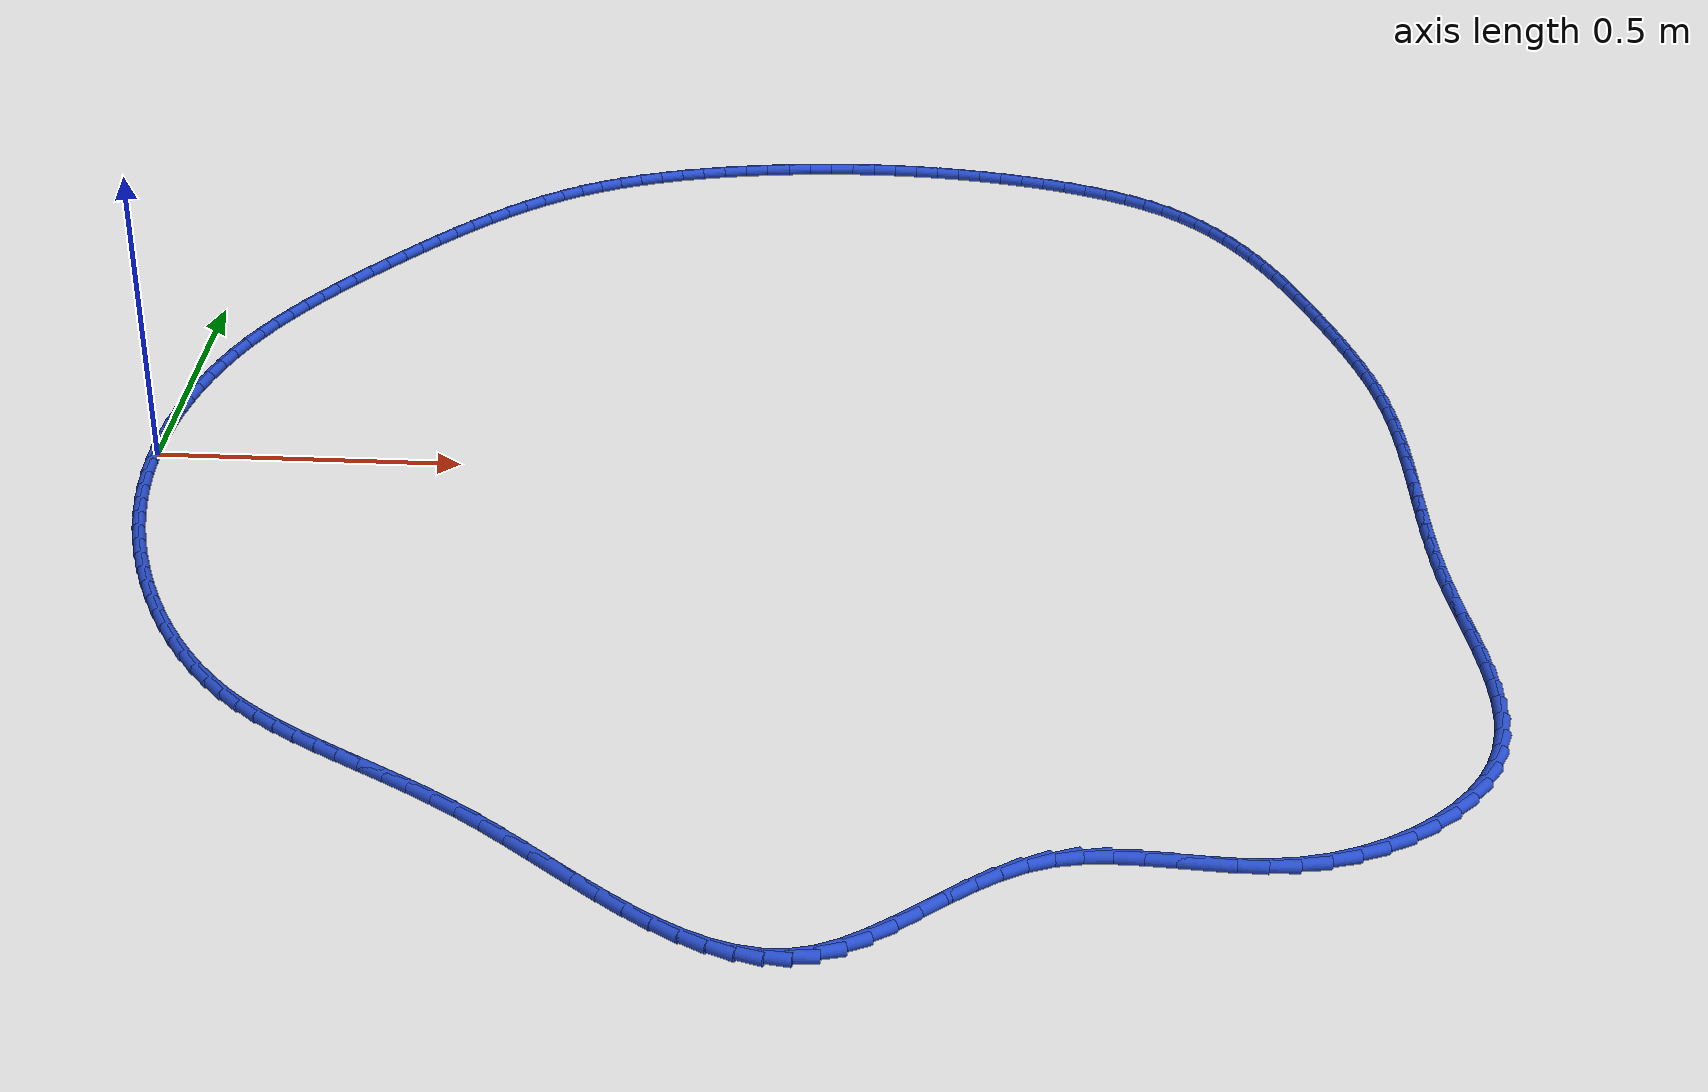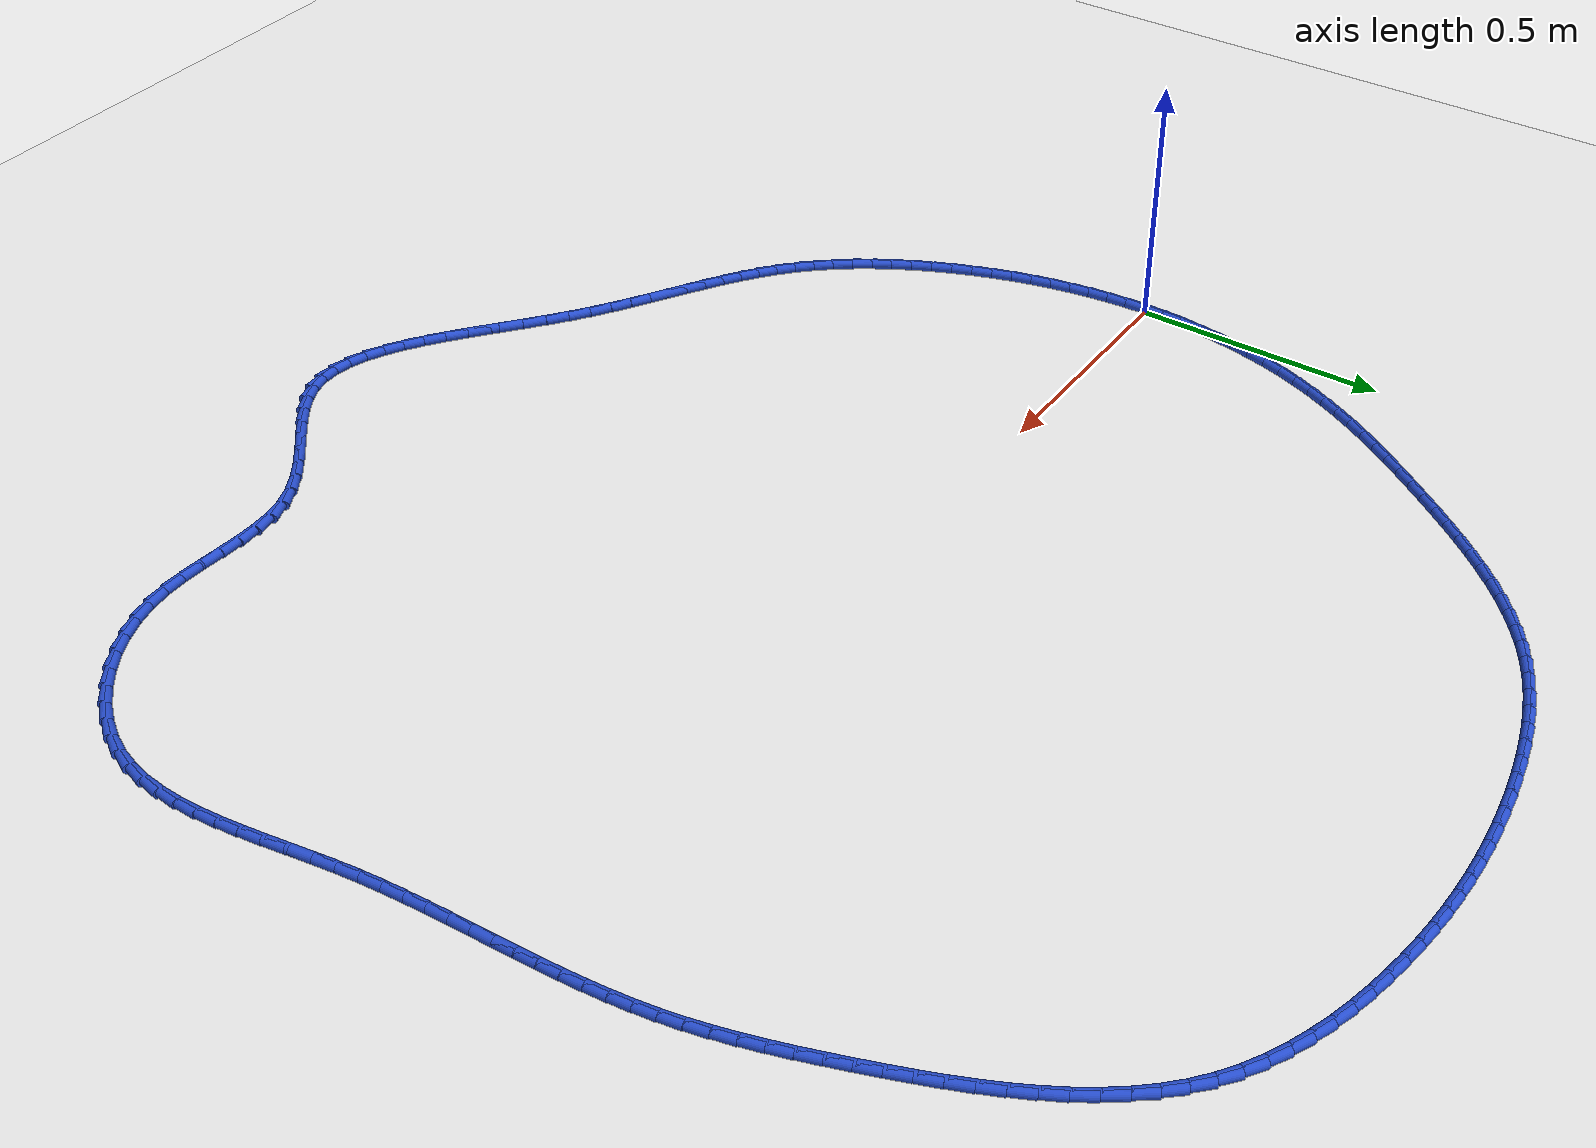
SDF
<sdf version="1.6">
 <world name="default">
  <light name="sun" type="directional">
   <pose>0 0 10 0 -0 0</pose>
   <diffuse>0.8 0.8 0.8 1</diffuse>
   <specular>0.2 0.2 0.2 1</specular>
   <attenuation>
    <range>1000</range>
    <constant>0.9</constant>
    <linear>0.01</linear>
    <quadratic>0.001</quadratic>
   </attenuation>
   <direction>-0.5 0.1 -0.9</direction>
  </light>
  <model name="ground_plane">
   <static>1</static>
   <link name="link">
    <collision name="collision">
     <geometry><plane><normal>0 0 1</normal><size>100 100</size></plane></geometry>
     <surface><friction><ode><mu>100</mu><mu2>50</mu2></ode></friction></surface>
    </collision>
    <visual name="visual">
     <cast_shadows>0</cast_shadows>
     <geometry><plane><normal>0 0 1</normal><size>100 100</size></plane></geometry>
     <material>
      <script><uri>file://media/materials/scripts/gazebo.material</uri><name>Gazebo/WhiteGlow</name></script>
     </material>
    </visual>
   </link>
  </model>
  <gravity>0 0 -9.8</gravity>
  <magnetic_field>6e-06 2.3e-05 -4.2e-05</magnetic_field>
  <atmosphere type="adiabatic"/>
  <physics name="default_physics" default="0" type="ode">
   <max_step_size>0.001</max_step_size>
   <real_time_factor>1</real_time_factor>
   <real_time_update_rate>1000</real_time_update_rate>
  </physics>
  <scene><ambient>0.4 0.4 0.4 1</ambient><background>0.7 0.7 0.7 1</background><shadows>1</shadows></scene>
  <spherical_coordinates>
   <surface_model>EARTH_WGS84</surface_model>
   <latitude_deg>0</latitude_deg>
   <longitude_deg>0</longitude_deg>
   <elevation>0</elevation>
   <heading_deg>0</heading_deg>
  </spherical_coordinates>
  <model name="line">
   <link name="link_0">
    <pose>1.5612511283791264e-17 4.85722573273506e-17 0.01 0 1.57 1.552494242766472</pose>
    <collision name="collision">
     <geometry><cylinder><radius>0.01</radius><length>0.08</length></cylinder></geometry>
    </collision>
    <visual name="visual">
     <material>
      <script><name>Gazebo/Blue</name><uri>file://media/materials/scripts/gazebo.material</uri></script>
     </material>
     <geometry><cylinder><radius>0.01</radius><length>0.08</length></cylinder></geometry>
    </visual>
   </link>
   <link name="link_1">
    <pose>0.0007561603239106624 0.04131091800515218 0.01 0 1.57 1.5110941361753982</pose>
    <collision name="collision">
     <geometry><cylinder><radius>0.01</radius><length>0.08</length></cylinder></geometry>
    </collision>
    <visual name="visual">
     <material>
      <script><name>Gazebo/Blue</name><uri>file://media/materials/scripts/gazebo.material</uri></script>
     </material>
     <geometry><cylinder><radius>0.01</radius><length>0.08</length></cylinder></geometry>
    </visual>
   </link>
   <link name="link_2">
    <pose>0.0032270958861729637 0.08264941962122437 0.01 0 1.57 1.4697142427487881</pose>
    <collision name="collision">
     <geometry><cylinder><radius>0.01</radius><length>0.08</length></cylinder></geometry>
    </collision>
    <visual name="visual">
     <material>
      <script><name>Gazebo/Blue</name><uri>file://media/materials/scripts/gazebo.material</uri></script>
     </material>
     <geometry><cylinder><radius>0.01</radius><length>0.08</length></cylinder></geometry>
    </visual>
   </link>
   <link name="link_3">
    <pose>0.007411543099879433 0.12390485953049359 0.01 0 1.57 1.4281658494729377</pose>
    <collision name="collision">
     <geometry><cylinder><radius>0.01</radius><length>0.08</length></cylinder></geometry>
    </collision>
    <visual name="visual">
     <material>
      <script><name>Gazebo/Blue</name><uri>file://media/materials/scripts/gazebo.material</uri></script>
     </material>
     <geometry><cylinder><radius>0.01</radius><length>0.08</length></cylinder></geometry>
    </visual>
   </link>
   <link name="link_4">
    <pose>0.013308238378122613 0.16496659241523676 0.01 0 1.57 1.3862621743135723</pose>
    <collision name="collision">
     <geometry><cylinder><radius>0.01</radius><length>0.08</length></cylinder></geometry>
    </collision>
    <visual name="visual">
     <material>
      <script><name>Gazebo/Blue</name><uri>file://media/materials/scripts/gazebo.material</uri></script>
     </material>
     <geometry><cylinder><radius>0.01</radius><length>0.08</length></cylinder></geometry>
    </visual>
   </link>
   <link name="link_5">
    <pose>0.02091591813399502 0.20572397295773076 0.01 0 1.57 1.3438181536379181</pose>
    <collision name="collision">
     <geometry><cylinder><radius>0.01</radius><length>0.08</length></cylinder></geometry>
    </collision>
    <visual name="visual">
     <material>
      <script><name>Gazebo/Blue</name><uri>file://media/materials/scripts/gazebo.material</uri></script>
     </material>
     <geometry><cylinder><radius>0.01</radius><length>0.08</length></cylinder></geometry>
    </visual>
   </link>
   <link name="link_6">
    <pose>0.03023331878058918 0.24606635584025255 0.01 0 1.57 1.3006505023268</pose>
    <collision name="collision">
     <geometry><cylinder><radius>0.01</radius><length>0.08</length></cylinder></geometry>
    </collision>
    <visual name="visual">
     <material>
      <script><name>Gazebo/Blue</name><uri>file://media/materials/scripts/gazebo.material</uri></script>
     </material>
     <geometry><cylinder><radius>0.01</radius><length>0.08</length></cylinder></geometry>
    </visual>
   </link>
   <link name="link_7">
    <pose>0.04125917673099763 0.28588309574507903 0.01 0 1.57 1.2565781655612556</pose>
    <collision name="collision">
     <geometry><cylinder><radius>0.01</radius><length>0.08</length></cylinder></geometry>
    </collision>
    <visual name="visual">
     <material>
      <script><name>Gazebo/Blue</name><uri>file://media/materials/scripts/gazebo.material</uri></script>
     </material>
     <geometry><cylinder><radius>0.01</radius><length>0.08</length></cylinder></geometry>
    </visual>
   </link>
   <link name="link_8">
    <pose>0.05399222839831289 0.32506354735448717 0.01 0 1.57 1.2114234558439276</pose>
    <collision name="collision">
     <geometry><cylinder><radius>0.01</radius><length>0.08</length></cylinder></geometry>
    </collision>
    <visual name="visual">
     <material>
      <script><name>Gazebo/Blue</name><uri>file://media/materials/scripts/gazebo.material</uri></script>
     </material>
     <geometry><cylinder><radius>0.01</radius><length>0.08</length></cylinder></geometry>
    </visual>
   </link>
   <link name="link_9">
    <pose>0.06843120546788965 0.36349707185075997 0.01 0 1.57 1.1659762774763802</pose>
    <collision name="collision">
     <geometry><cylinder><radius>0.01</radius><length>0.08</length></cylinder></geometry>
    </collision>
    <visual name="visual">
     <material>
      <script><name>Gazebo/Blue</name><uri>file://media/materials/scripts/gazebo.material</uri></script>
     </material>
     <geometry><cylinder><radius>0.01</radius><length>0.08</length></cylinder></geometry>
    </visual>
   </link>
   <link name="link_10">
    <pose>0.08454787958623389 0.40111009685829574 0.01 0 1.57 1.1234726091473382</pose>
    <collision name="collision">
     <geometry><cylinder><radius>0.01</radius><length>0.08</length></cylinder></geometry>
    </collision>
    <visual name="visual">
     <material>
      <script><name>Gazebo/Blue</name><uri>file://media/materials/scripts/gazebo.material</uri></script>
     </material>
     <geometry><cylinder><radius>0.01</radius><length>0.08</length></cylinder></geometry>
    </visual>
   </link>
   <link name="link_11">
    <pose>0.10222369289270093 0.43795324097417 0.01 0 1.57 1.0847761233856386</pose>
    <collision name="collision">
     <geometry><cylinder><radius>0.01</radius><length>0.08</length></cylinder></geometry>
    </collision>
    <visual name="visual">
     <material>
      <script><name>Gazebo/Blue</name><uri>file://media/materials/scripts/gazebo.material</uri></script>
     </material>
     <geometry><cylinder><radius>0.01</radius><length>0.08</length></cylinder></geometry>
    </visual>
   </link>
   <link name="link_12">
    <pose>0.12132119100321208 0.4741031029839879 0.01 0 1.57 1.0500169967786583</pose>
    <collision name="collision">
     <geometry><cylinder><radius>0.01</radius><length>0.08</length></cylinder></geometry>
    </collision>
    <visual name="visual">
     <material>
      <script><name>Gazebo/Blue</name><uri>file://media/materials/scripts/gazebo.material</uri></script>
     </material>
     <geometry><cylinder><radius>0.01</radius><length>0.08</length></cylinder></geometry>
    </visual>
   </link>
   <link name="link_13">
    <pose>0.1417029195336885 0.5096362816733543 0.01 0 1.57 1.0192596497147077</pose>
    <collision name="collision">
     <geometry><cylinder><radius>0.01</radius><length>0.08</length></cylinder></geometry>
    </collision>
    <visual name="visual">
     <material>
      <script><name>Gazebo/Blue</name><uri>file://media/materials/scripts/gazebo.material</uri></script>
     </material>
     <geometry><cylinder><radius>0.01</radius><length>0.08</length></cylinder></geometry>
    </visual>
   </link>
   <link name="link_14">
    <pose>0.16323142410005137 0.5446293758278742 0.01 0 1.57 0.9925182560057357</pose>
    <collision name="collision">
     <geometry><cylinder><radius>0.01</radius><length>0.08</length></cylinder></geometry>
    </collision>
    <visual name="visual">
     <material>
      <script><name>Gazebo/Blue</name><uri>file://media/materials/scripts/gazebo.material</uri></script>
     </material>
     <geometry><cylinder><radius>0.01</radius><length>0.08</length></cylinder></geometry>
    </visual>
   </link>
   <link name="link_15">
    <pose>0.18576925031822195 0.5791589842331523 0.01 0 1.57 0.9697715484052462</pose>
    <collision name="collision">
     <geometry><cylinder><radius>0.01</radius><length>0.08</length></cylinder></geometry>
    </collision>
    <visual name="visual">
     <material>
      <script><name>Gazebo/Blue</name><uri>file://media/materials/scripts/gazebo.material</uri></script>
     </material>
     <geometry><cylinder><radius>0.01</radius><length>0.08</length></cylinder></geometry>
    </visual>
   </link>
   <link name="link_16">
    <pose>0.2091789438041216 0.6133017056747944 0.01 0 1.57 0.9509759353911914</pose>
    <collision name="collision">
     <geometry><cylinder><radius>0.01</radius><length>0.08</length></cylinder></geometry>
    </collision>
    <visual name="visual">
     <material>
      <script><name>Gazebo/Blue</name><uri>file://media/materials/scripts/gazebo.material</uri></script>
     </material>
     <geometry><cylinder><radius>0.01</radius><length>0.08</length></cylinder></geometry>
    </visual>
   </link>
   <link name="link_17">
    <pose>0.23332305017367136 0.6471341389384044 0.01 0 1.57 0.9360764523887087</pose>
    <collision name="collision">
     <geometry><cylinder><radius>0.01</radius><length>0.08</length></cylinder></geometry>
    </collision>
    <visual name="visual">
     <material>
      <script><name>Gazebo/Blue</name><uri>file://media/materials/scripts/gazebo.material</uri></script>
     </material>
     <geometry><cylinder><radius>0.01</radius><length>0.08</length></cylinder></geometry>
    </visual>
   </link>
   <link name="link_18">
    <pose>0.25806411504279236 0.6807328828095877 0.01 0 1.57 0.9249828219837867</pose>
    <collision name="collision">
     <geometry><cylinder><radius>0.01</radius><length>0.08</length></cylinder></geometry>
    </collision>
    <visual name="visual">
     <material>
      <script><name>Gazebo/Blue</name><uri>file://media/materials/scripts/gazebo.material</uri></script>
     </material>
     <geometry><cylinder><radius>0.01</radius><length>0.08</length></cylinder></geometry>
    </visual>
   </link>
   <link name="link_19">
    <pose>0.2832655937795968 0.7141734745171459 0.01 0 1.57 0.9147614266622315</pose>
    <collision name="collision">
     <geometry><cylinder><radius>0.01</radius><length>0.08</length></cylinder></geometry>
    </collision>
    <visual name="visual">
     <material>
      <script><name>Gazebo/Blue</name><uri>file://media/materials/scripts/gazebo.material</uri></script>
     </material>
     <geometry><cylinder><radius>0.01</radius><length>0.08</length></cylinder></geometry>
    </visual>
   </link>
   <link name="link_20">
    <pose>0.30887136092074996 0.7474376130816518 0.01 0 1.57 0.9002645387950842</pose>
    <collision name="collision">
     <geometry><cylinder><radius>0.01</radius><length>0.08</length></cylinder></geometry>
    </collision>
    <visual name="visual">
     <material>
      <script><name>Gazebo/Blue</name><uri>file://media/materials/scripts/gazebo.material</uri></script>
     </material>
     <geometry><cylinder><radius>0.01</radius><length>0.08</length></cylinder></geometry>
    </visual>
   </link>
   <link name="link_21">
    <pose>0.3349676275952109 0.780340910121552 0.01 0 1.57 0.8808826945066012</pose>
    <collision name="collision">
     <geometry><cylinder><radius>0.01</radius><length>0.08</length></cylinder></geometry>
    </collision>
    <visual name="visual">
     <material>
      <script><name>Gazebo/Blue</name><uri>file://media/materials/scripts/gazebo.material</uri></script>
     </material>
     <geometry><cylinder><radius>0.01</radius><length>0.08</length></cylinder></geometry>
    </visual>
   </link>
   <link name="link_22">
    <pose>0.3616551782339264 0.8126819721982758 0.01 0 1.57 0.8564794366318301</pose>
    <collision name="collision">
     <geometry><cylinder><radius>0.01</radius><length>0.08</length></cylinder></geometry>
    </collision>
    <visual name="visual">
     <material>
      <script><name>Gazebo/Blue</name><uri>file://media/materials/scripts/gazebo.material</uri></script>
     </material>
     <geometry><cylinder><radius>0.01</radius><length>0.08</length></cylinder></geometry>
    </visual>
   </link>
   <link name="link_23">
    <pose>0.38903479726784346 0.8442594058732529 0.01 0 1.57 0.8268806010101626</pose>
    <collision name="collision">
     <geometry><cylinder><radius>0.01</radius><length>0.08</length></cylinder></geometry>
    </collision>
    <visual name="visual">
     <material>
      <script><name>Gazebo/Blue</name><uri>file://media/materials/scripts/gazebo.material</uri></script>
     </material>
     <geometry><cylinder><radius>0.01</radius><length>0.08</length></cylinder></geometry>
    </visual>
   </link>
   <link name="link_24">
    <pose>0.417207269127909 0.8748718177079123 0.01 0 1.57 0.7918905310314991</pose>
    <collision name="collision">
     <geometry><cylinder><radius>0.01</radius><length>0.08</length></cylinder></geometry>
    </collision>
    <visual name="visual">
     <material>
      <script><name>Gazebo/Blue</name><uri>file://media/materials/scripts/gazebo.material</uri></script>
     </material>
     <geometry><cylinder><radius>0.01</radius><length>0.08</length></cylinder></geometry>
    </visual>
   </link>
   <link name="link_25">
    <pose>0.4462733782450701 0.9043178142636841 0.01 0 1.57 0.7513145899885959</pose>
    <collision name="collision">
     <geometry><cylinder><radius>0.01</radius><length>0.08</length></cylinder></geometry>
    </collision>
    <visual name="visual">
     <material>
      <script><name>Gazebo/Blue</name><uri>file://media/materials/scripts/gazebo.material</uri></script>
     </material>
     <geometry><cylinder><radius>0.01</radius><length>0.08</length></cylinder></geometry>
    </visual>
   </link>
   <link name="link_26">
    <pose>0.47633390905027334 0.9323960021019971 0.01 0 1.57 0.7049896891268153</pose>
    <collision name="collision">
     <geometry><cylinder><radius>0.01</radius><length>0.08</length></cylinder></geometry>
    </collision>
    <visual name="visual">
     <material>
      <script><name>Gazebo/Blue</name><uri>file://media/materials/scripts/gazebo.material</uri></script>
     </material>
     <geometry><cylinder><radius>0.01</radius><length>0.08</length></cylinder></geometry>
    </visual>
   </link>
   <link name="link_27">
    <pose>0.5074896459744659 0.9589049877842813 0.01 0 1.57 0.6528238842404018</pose>
    <collision name="collision">
     <geometry><cylinder><radius>0.01</radius><length>0.08</length></cylinder></geometry>
    </collision>
    <visual name="visual">
     <material>
      <script><name>Gazebo/Blue</name><uri>file://media/materials/scripts/gazebo.material</uri></script>
     </material>
     <geometry><cylinder><radius>0.01</radius><length>0.08</length></cylinder></geometry>
    </visual>
   </link>
   <link name="link_28">
    <pose>0.5398413734485945 0.9836433778719655 0.01 0 1.57 0.5948444535056344</pose>
    <collision name="collision">
     <geometry><cylinder><radius>0.01</radius><length>0.08</length></cylinder></geometry>
    </collision>
    <visual name="visual">
     <material>
      <script><name>Gazebo/Blue</name><uri>file://media/materials/scripts/gazebo.material</uri></script>
     </material>
     <geometry><cylinder><radius>0.01</radius><length>0.08</length></cylinder></geometry>
    </visual>
   </link>
   <link name="link_29">
    <pose>0.5734898759036063 1.0064097789264799 0.01 0 1.57 0.5313811504077449</pose>
    <collision name="collision">
     <geometry><cylinder><radius>0.01</radius><length>0.08</length></cylinder></geometry>
    </collision>
    <visual name="visual">
     <material>
      <script><name>Gazebo/Blue</name><uri>file://media/materials/scripts/gazebo.material</uri></script>
     </material>
     <geometry><cylinder><radius>0.01</radius><length>0.08</length></cylinder></geometry>
    </visual>
   </link>
   <link name="link_30">
    <pose>0.6085325280339045 1.0270069322213067 0.01 0 1.57 0.46730874825611696</pose>
    <collision name="collision">
     <geometry><cylinder><radius>0.01</radius><length>0.08</length></cylinder></geometry>
    </collision>
    <visual name="visual">
     <material>
      <script><name>Gazebo/Blue</name><uri>file://media/materials/scripts/gazebo.material</uri></script>
     </material>
     <geometry><cylinder><radius>0.01</radius><length>0.08</length></cylinder></geometry>
    </visual>
   </link>
   <link name="link_31">
    <pose>0.6449479389739791 1.0453815964300228 0.01 0 1.57 0.40834525245156716</pose>
    <collision name="collision">
     <geometry><cylinder><radius>0.01</radius><length>0.08</length></cylinder></geometry>
    </collision>
    <visual name="visual">
     <material>
      <script><name>Gazebo/Blue</name><uri>file://media/materials/scripts/gazebo.material</uri></script>
     </material>
     <geometry><cylinder><radius>0.01</radius><length>0.08</length></cylinder></geometry>
    </visual>
   </link>
   <link name="link_32">
    <pose>0.682567971095135 1.061658478171064 0.01 0 1.57 0.35472746600115135</pose>
    <collision name="collision">
     <geometry><cylinder><radius>0.01</radius><length>0.08</length></cylinder></geometry>
    </collision>
    <visual name="visual">
     <material>
      <script><name>Gazebo/Blue</name><uri>file://media/materials/scripts/gazebo.material</uri></script>
     </material>
     <geometry><cylinder><radius>0.01</radius><length>0.08</length></cylinder></geometry>
    </visual>
   </link>
   <link name="link_33">
    <pose>0.7212154021585478 1.0759733002356735 0.01 0 1.57 0.30623697293449614</pose>
    <collision name="collision">
     <geometry><cylinder><radius>0.01</radius><length>0.08</length></cylinder></geometry>
    </collision>
    <visual name="visual">
     <material>
      <script><name>Gazebo/Blue</name><uri>file://media/materials/scripts/gazebo.material</uri></script>
     </material>
     <geometry><cylinder><radius>0.01</radius><length>0.08</length></cylinder></geometry>
    </visual>
   </link>
   <link name="link_34">
    <pose>0.7607130099253938 1.0884617854150944 0.01 0 1.57 0.26259358930149873</pose>
    <collision name="collision">
     <geometry><cylinder><radius>0.01</radius><length>0.08</length></cylinder></geometry>
    </collision>
    <visual name="visual">
     <material>
      <script><name>Gazebo/Blue</name><uri>file://media/materials/scripts/gazebo.material</uri></script>
     </material>
     <geometry><cylinder><radius>0.01</radius><length>0.08</length></cylinder></geometry>
    </visual>
   </link>
   <link name="link_35">
    <pose>0.8008835721568484 1.09925965650057 0.01 0 1.57 0.22349156907910278</pose>
    <collision name="collision">
     <geometry><cylinder><radius>0.01</radius><length>0.08</length></cylinder></geometry>
    </collision>
    <visual name="visual">
     <material>
      <script><name>Gazebo/Blue</name><uri>file://media/materials/scripts/gazebo.material</uri></script>
     </material>
     <geometry><cylinder><radius>0.01</radius><length>0.08</length></cylinder></geometry>
    </visual>
   </link>
   <link name="link_36">
    <pose>0.8415498666140879 1.1085026362833432 0.01 0 1.57 0.18862602162037828</pose>
    <collision name="collision">
     <geometry><cylinder><radius>0.01</radius><length>0.08</length></cylinder></geometry>
    </collision>
    <visual name="visual">
     <material>
      <script><name>Gazebo/Blue</name><uri>file://media/materials/scripts/gazebo.material</uri></script>
     </material>
     <geometry><cylinder><radius>0.01</radius><length>0.08</length></cylinder></geometry>
    </visual>
   </link>
   <link name="link_37">
    <pose>0.8825346710582874 1.1163264475546575 0.01 0 1.57 0.15771125868965835</pose>
    <collision name="collision">
     <geometry><cylinder><radius>0.01</radius><length>0.08</length></cylinder></geometry>
    </collision>
    <visual name="visual">
     <material>
      <script><name>Gazebo/Blue</name><uri>file://media/materials/scripts/gazebo.material</uri></script>
     </material>
     <geometry><cylinder><radius>0.01</radius><length>0.08</length></cylinder></geometry>
    </visual>
   </link>
   <link name="link_38">
    <pose>0.9236607650763194 1.1228668115489195 0.01 0 1.57 0.1296892411614359</pose>
    <collision name="collision">
     <geometry><cylinder><radius>0.01</radius><length>0.08</length></cylinder></geometry>
    </collision>
    <visual name="visual">
     <material>
      <script><name>Gazebo/Blue</name><uri>file://media/materials/scripts/gazebo.material</uri></script>
     </material>
     <geometry><cylinder><radius>0.01</radius><length>0.08</length></cylinder></geometry>
    </visual>
   </link>
   <link name="link_39">
    <pose>0.9647851110631582 1.1282303005868752 0.01 0 1.57 0.10158019451259925</pose>
    <collision name="collision">
     <geometry><cylinder><radius>0.01</radius><length>0.08</length></cylinder></geometry>
    </collision>
    <visual name="visual">
     <material>
      <script><name>Gazebo/Blue</name><uri>file://media/materials/scripts/gazebo.material</uri></script>
     </material>
     <geometry><cylinder><radius>0.01</radius><length>0.08</length></cylinder></geometry>
    </visual>
   </link>
   <link name="link_40">
    <pose>1.0058862820261167 1.1324197852328615 0.01 0 1.57 0.07277865001213683</pose>
    <collision name="collision">
     <geometry><cylinder><radius>0.01</radius><length>0.08</length></cylinder></geometry>
    </collision>
    <visual name="visual">
     <material>
      <script><name>Gazebo/Blue</name><uri>file://media/materials/scripts/gazebo.material</uri></script>
     </material>
     <geometry><cylinder><radius>0.01</radius><length>0.08</length></cylinder></geometry>
    </visual>
   </link>
   <link name="link_41">
    <pose>1.0469698833413086 1.1354150845751108 0.01 0 1.57 0.04333448393730779</pose>
    <collision name="collision">
     <geometry><cylinder><radius>0.01</radius><length>0.08</length></cylinder></geometry>
    </collision>
    <visual name="visual">
     <material>
      <script><name>Gazebo/Blue</name><uri>file://media/materials/scripts/gazebo.material</uri></script>
     </material>
     <geometry><cylinder><radius>0.01</radius><length>0.08</length></cylinder></geometry>
    </visual>
   </link>
   <link name="link_42">
    <pose>1.0880415203848464 1.1371960177018554 0.01 0 1.57 0.013304518685758722</pose>
    <collision name="collision">
     <geometry><cylinder><radius>0.01</radius><length>0.08</length></cylinder></geometry>
    </collision>
    <visual name="visual">
     <material>
      <script><name>Gazebo/Blue</name><uri>file://media/materials/scripts/gazebo.material</uri></script>
     </material>
     <geometry><cylinder><radius>0.01</radius><length>0.08</length></cylinder></geometry>
    </visual>
   </link>
   <link name="link_43">
    <pose>1.1291067985328433 1.1377424037013266 0.01 0 1.57 -0.017247777832717304</pose>
    <collision name="collision">
     <geometry><cylinder><radius>0.01</radius><length>0.08</length></cylinder></geometry>
    </collision>
    <visual name="visual">
     <material>
      <script><name>Gazebo/Blue</name><uri>file://media/materials/scripts/gazebo.material</uri></script>
     </material>
     <geometry><cylinder><radius>0.01</radius><length>0.08</length></cylinder></geometry>
    </visual>
   </link>
   <link name="link_44">
    <pose>1.1701713231614126 1.1370340616617582 0.01 0 1.57 -0.048252778582215695</pose>
    <collision name="collision">
     <geometry><cylinder><radius>0.01</radius><length>0.08</length></cylinder></geometry>
    </collision>
    <visual name="visual">
     <material>
      <script><name>Gazebo/Blue</name><uri>file://media/materials/scripts/gazebo.material</uri></script>
     </material>
     <geometry><cylinder><radius>0.01</radius><length>0.08</length></cylinder></geometry>
    </visual>
   </link>
   <link name="link_45">
    <pose>1.2112406996466671 1.1350508106713817 0.01 0 1.57 -0.07963536946877868</pose>
    <collision name="collision">
     <geometry><cylinder><radius>0.01</radius><length>0.08</length></cylinder></geometry>
    </collision>
    <visual name="visual">
     <material>
      <script><name>Gazebo/Blue</name><uri>file://media/materials/scripts/gazebo.material</uri></script>
     </material>
     <geometry><cylinder><radius>0.01</radius><length>0.08</length></cylinder></geometry>
    </visual>
   </link>
   <link name="link_46">
    <pose>1.2523205333647196 1.1317724698184297 0.01 0 1.57 -0.11131579744496883</pose>
    <collision name="collision">
     <geometry><cylinder><radius>0.01</radius><length>0.08</length></cylinder></geometry>
    </collision>
    <visual name="visual">
     <material>
      <script><name>Gazebo/Blue</name><uri>file://media/materials/scripts/gazebo.material</uri></script>
     </material>
     <geometry><cylinder><radius>0.01</radius><length>0.08</length></cylinder></geometry>
    </visual>
   </link>
   <link name="link_47">
    <pose>1.2934164296916832 1.1271788581911333 0.01 0 1.57 -0.14321067508054178</pose>
    <collision name="collision">
     <geometry><cylinder><radius>0.01</radius><length>0.08</length></cylinder></geometry>
    </collision>
    <visual name="visual">
     <material>
      <script><name>Gazebo/Blue</name><uri>file://media/materials/scripts/gazebo.material</uri></script>
     </material>
     <geometry><cylinder><radius>0.01</radius><length>0.08</length></cylinder></geometry>
    </visual>
   </link>
   <link name="link_48">
    <pose>1.334533994003671 1.1212497948777258 0.01 0 1.57 -0.17523411257376645</pose>
    <collision name="collision">
     <geometry><cylinder><radius>0.01</radius><length>0.08</length></cylinder></geometry>
    </collision>
    <visual name="visual">
     <material>
      <script><name>Gazebo/Blue</name><uri>file://media/materials/scripts/gazebo.material</uri></script>
     </material>
     <geometry><cylinder><radius>0.01</radius><length>0.08</length></cylinder></geometry>
    </visual>
   </link>
   <link name="link_49">
    <pose>1.375678831676796 1.1139650989664391 0.01 0 1.57 -0.2077585654538869</pose>
    <collision name="collision">
     <geometry><cylinder><radius>0.01</radius><length>0.08</length></cylinder></geometry>
    </collision>
    <visual name="visual">
     <material>
      <script><name>Gazebo/Blue</name><uri>file://media/materials/scripts/gazebo.material</uri></script>
     </material>
     <geometry><cylinder><radius>0.01</radius><length>0.08</length></cylinder></geometry>
    </visual>
   </link>
   <link name="link_50">
    <pose>1.4168285381660686 1.105290728610439 0.01 0 1.57 -0.24415226316200395</pose>
    <collision name="collision">
     <geometry><cylinder><radius>0.01</radius><length>0.08</length></cylinder></geometry>
    </collision>
    <visual name="visual">
     <material>
      <script><name>Gazebo/Blue</name><uri>file://media/materials/scripts/gazebo.material</uri></script>
     </material>
     <geometry><cylinder><radius>0.01</radius><length>0.08</length></cylinder></geometry>
    </visual>
   </link>
   <link name="link_51">
    <pose>1.4577606398974763 1.0950936361924035 0.01 0 1.57 -0.2863271445213465</pose>
    <collision name="collision">
     <geometry><cylinder><radius>0.01</radius><length>0.08</length></cylinder></geometry>
    </collision>
    <visual name="visual">
     <material>
      <script><name>Gazebo/Blue</name><uri>file://media/materials/scripts/gazebo.material</uri></script>
     </material>
     <geometry><cylinder><radius>0.01</radius><length>0.08</length></cylinder></geometry>
    </visual>
   </link>
   <link name="link_52">
    <pose>1.4981656378658175 1.0831977088594298 0.01 0 1.57 -0.33492295416491824</pose>
    <collision name="collision">
     <geometry><cylinder><radius>0.01</radius><length>0.08</length></cylinder></geometry>
    </collision>
    <visual name="visual">
     <material>
      <script><name>Gazebo/Blue</name><uri>file://media/materials/scripts/gazebo.material</uri></script>
     </material>
     <geometry><cylinder><radius>0.01</radius><length>0.08</length></cylinder></geometry>
    </visual>
   </link>
   <link name="link_53">
    <pose>1.537733676189212 1.0694266571553186 0.01 0 1.57 -0.39065070604968116</pose>
    <collision name="collision">
     <geometry><cylinder><radius>0.01</radius><length>0.08</length></cylinder></geometry>
    </collision>
    <visual name="visual">
     <material>
      <script><name>Gazebo/Blue</name><uri>file://media/materials/scripts/gazebo.material</uri></script>
     </material>
     <geometry><cylinder><radius>0.01</radius><length>0.08</length></cylinder></geometry>
    </visual>
   </link>
   <link name="link_54">
    <pose>1.5761548989857816 1.0536041916238692 0.01 0 1.57 -0.45425214072454867</pose>
    <collision name="collision">
     <geometry><cylinder><radius>0.01</radius><length>0.08</length></cylinder></geometry>
    </collision>
    <visual name="visual">
     <material>
      <script><name>Gazebo/Blue</name><uri>file://media/materials/scripts/gazebo.material</uri></script>
     </material>
     <geometry><cylinder><radius>0.01</radius><length>0.08</length></cylinder></geometry>
    </visual>
   </link>
   <link name="link_55">
    <pose>1.6131194503736483 1.0355540228088822 0.01 0 1.57 -0.5264190329960129</pose>
    <collision name="collision">
     <geometry><cylinder><radius>0.01</radius><length>0.08</length></cylinder></geometry>
    </collision>
    <visual name="visual">
     <material>
      <script><name>Gazebo/Blue</name><uri>file://media/materials/scripts/gazebo.material</uri></script>
     </material>
     <geometry><cylinder><radius>0.01</radius><length>0.08</length></cylinder></geometry>
    </visual>
   </link>
   <link name="link_56">
    <pose>1.6483174744709315 1.0150998612541573 0.01 0 1.57 -0.6076657120524813</pose>
    <collision name="collision">
     <geometry><cylinder><radius>0.01</radius><length>0.08</length></cylinder></geometry>
    </collision>
    <visual name="visual">
     <material>
      <script><name>Gazebo/Blue</name><uri>file://media/materials/scripts/gazebo.material</uri></script>
     </material>
     <geometry><cylinder><radius>0.01</radius><length>0.08</length></cylinder></geometry>
    </visual>
   </link>
   <link name="link_57">
    <pose>1.681439115395754 0.9920654175034952 0.01 0 1.57 -0.6964221804945231</pose>
    <collision name="collision">
     <geometry><cylinder><radius>0.01</radius><length>0.08</length></cylinder></geometry>
    </collision>
    <visual name="visual">
     <material>
      <script><name>Gazebo/Blue</name><uri>file://media/materials/scripts/gazebo.material</uri></script>
     </material>
     <geometry><cylinder><radius>0.01</radius><length>0.08</length></cylinder></geometry>
    </visual>
   </link>
   <link name="link_58">
    <pose>1.7122262675955777 0.9663214893765767 0.01 0 1.57 -0.7818830817145667</pose>
    <collision name="collision">
     <geometry><cylinder><radius>0.01</radius><length>0.08</length></cylinder></geometry>
    </collision>
    <visual name="visual">
     <material>
      <script><name>Gazebo/Blue</name><uri>file://media/materials/scripts/gazebo.material</uri></script>
     </material>
     <geometry><cylinder><radius>0.01</radius><length>0.08</length></cylinder></geometry>
    </visual>
   </link>
   <link name="link_59">
    <pose>1.7407285555169023 0.9380188761451728 0.01 0 1.57 -0.8594376618038342</pose>
    <collision name="collision">
     <geometry><cylinder><radius>0.01</radius><length>0.08</length></cylinder></geometry>
    </collision>
    <visual name="visual">
     <material>
      <script><name>Gazebo/Blue</name><uri>file://media/materials/scripts/gazebo.material</uri></script>
     </material>
     <geometry><cylinder><radius>0.01</radius><length>0.08</length></cylinder></geometry>
    </visual>
   </link>
   <link name="link_60">
    <pose>1.767108897502782 0.9074114624339515 0.01 0 1.57 -0.9287103522166293</pose>
    <collision name="collision">
     <geometry><cylinder><radius>0.01</radius><length>0.08</length></cylinder></geometry>
    </collision>
    <visual name="visual">
     <material>
      <script><name>Gazebo/Blue</name><uri>file://media/materials/scripts/gazebo.material</uri></script>
     </material>
     <geometry><cylinder><radius>0.01</radius><length>0.08</length></cylinder></geometry>
    </visual>
   </link>
   <link name="link_61">
    <pose>1.791530388591372 0.8747532936412619 0.01 0 1.57 -0.9897413864450195</pose>
    <collision name="collision">
     <geometry><cylinder><radius>0.01</radius><length>0.08</length></cylinder></geometry>
    </collision>
    <visual name="visual">
     <material>
      <script><name>Gazebo/Blue</name><uri>file://media/materials/scripts/gazebo.material</uri></script>
     </material>
     <geometry><cylinder><radius>0.01</radius><length>0.08</length></cylinder></geometry>
    </visual>
   </link>
   <link name="link_62">
    <pose>1.8141561238208244 0.8402984151654523 0.01 0 1.57 -1.0428357217157629</pose>
    <collision name="collision">
     <geometry><cylinder><radius>0.01</radius><length>0.08</length></cylinder></geometry>
    </collision>
    <visual name="visual">
     <material>
      <script><name>Gazebo/Blue</name><uri>file://media/materials/scripts/gazebo.material</uri></script>
     </material>
     <geometry><cylinder><radius>0.01</radius><length>0.08</length></cylinder></geometry>
    </visual>
   </link>
   <link name="link_63">
    <pose>1.835149198229295 0.8043008724048719 0.01 0 1.57 -1.0884374734652231</pose>
    <collision name="collision">
     <geometry><cylinder><radius>0.01</radius><length>0.08</length></cylinder></geometry>
    </collision>
    <visual name="visual">
     <material>
      <script><name>Gazebo/Blue</name><uri>file://media/materials/scripts/gazebo.material</uri></script>
     </material>
     <geometry><cylinder><radius>0.01</radius><length>0.08</length></cylinder></geometry>
    </visual>
   </link>
   <link name="link_64">
    <pose>1.8546727068549367 0.76701471075787 0.01 0 1.57 -1.1270352909015737</pose>
    <collision name="collision">
     <geometry><cylinder><radius>0.01</radius><length>0.08</length></cylinder></geometry>
    </collision>
    <visual name="visual">
     <material>
      <script><name>Gazebo/Blue</name><uri>file://media/materials/scripts/gazebo.material</uri></script>
     </material>
     <geometry><cylinder><radius>0.01</radius><length>0.08</length></cylinder></geometry>
    </visual>
   </link>
   <link name="link_65">
    <pose>1.8728897447359043 0.7286939756227946 0.01 0 1.57 -1.1590974973085162</pose>
    <collision name="collision">
     <geometry><cylinder><radius>0.01</radius><length>0.08</length></cylinder></geometry>
    </collision>
    <visual name="visual">
     <material>
      <script><name>Gazebo/Blue</name><uri>file://media/materials/scripts/gazebo.material</uri></script>
     </material>
     <geometry><cylinder><radius>0.01</radius><length>0.08</length></cylinder></geometry>
    </visual>
   </link>
   <link name="link_66">
    <pose>1.8899634069103515 0.6895927123979946 0.01 0 1.57 -1.1850304166883414</pose>
    <collision name="collision">
     <geometry><cylinder><radius>0.01</radius><length>0.08</length></cylinder></geometry>
    </collision>
    <visual name="visual">
     <material>
      <script><name>Gazebo/Blue</name><uri>file://media/materials/scripts/gazebo.material</uri></script>
     </material>
     <geometry><cylinder><radius>0.01</radius><length>0.08</length></cylinder></geometry>
    </visual>
   </link>
   <link name="link_67">
    <pose>1.9060567884164326 0.6499649664818192 0.01 0 1.57 -1.205152310493083</pose>
    <collision name="collision">
     <geometry><cylinder><radius>0.01</radius><length>0.08</length></cylinder></geometry>
    </collision>
    <visual name="visual">
     <material>
      <script><name>Gazebo/Blue</name><uri>file://media/materials/scripts/gazebo.material</uri></script>
     </material>
     <geometry><cylinder><radius>0.01</radius><length>0.08</length></cylinder></geometry>
    </visual>
   </link>
   <link name="link_68">
    <pose>1.921332984292301 0.6100647832726166 0.01 0 1.57 -1.2196763027260304</pose>
    <collision name="collision">
     <geometry><cylinder><radius>0.01</radius><length>0.08</length></cylinder></geometry>
    </collision>
    <visual name="visual">
     <material>
      <script><name>Gazebo/Blue</name><uri>file://media/materials/scripts/gazebo.material</uri></script>
     </material>
     <geometry><cylinder><radius>0.01</radius><length>0.08</length></cylinder></geometry>
    </visual>
   </link>
   <link name="link_69">
    <pose>1.9359550895761122 0.5701462081687366 0.01 0 1.57 -1.2300650007393579</pose>
    <collision name="collision">
     <geometry><cylinder><radius>0.01</radius><length>0.08</length></cylinder></geometry>
    </collision>
    <visual name="visual">
     <material>
      <script><name>Gazebo/Blue</name><uri>file://media/materials/scripts/gazebo.material</uri></script>
     </material>
     <geometry><cylinder><radius>0.01</radius><length>0.08</length></cylinder></geometry>
    </visual>
   </link>
   <link name="link_70">
    <pose>1.9500407133650044 0.5304191474286275 0.01 0 1.57 -1.2429131837614549</pose>
    <collision name="collision">
     <geometry><cylinder><radius>0.01</radius><length>0.08</length></cylinder></geometry>
    </collision>
    <visual name="visual">
     <material>
      <script><name>Gazebo/Blue</name><uri>file://media/materials/scripts/gazebo.material</uri></script>
     </material>
     <geometry><cylinder><radius>0.01</radius><length>0.08</length></cylinder></geometry>
    </visual>
   </link>
   <link name="link_71">
    <pose>1.9634896688784405 0.4908821601889617 0.01 0 1.57 -1.2602811705988675</pose>
    <collision name="collision">
     <geometry><cylinder><radius>0.01</radius><length>0.08</length></cylinder></geometry>
    </collision>
    <visual name="visual">
     <material>
      <script><name>Gazebo/Blue</name><uri>file://media/materials/scripts/gazebo.material</uri></script>
     </material>
     <geometry><cylinder><radius>0.01</radius><length>0.08</length></cylinder></geometry>
    </visual>
   </link>
   <link name="link_72">
    <pose>1.9761366584740478 0.4514706226033771 0.01 0 1.57 -1.2822680899109813</pose>
    <collision name="collision">
     <geometry><cylinder><radius>0.01</radius><length>0.08</length></cylinder></geometry>
    </collision>
    <visual name="visual">
     <material>
      <script><name>Gazebo/Blue</name><uri>file://media/materials/scripts/gazebo.material</uri></script>
     </material>
     <geometry><cylinder><radius>0.01</radius><length>0.08</length></cylinder></geometry>
    </visual>
   </link>
   <link name="link_73">
    <pose>1.9878163727872293 0.4121198994503703 0.01 0 1.57 -1.308946882892289</pose>
    <collision name="collision">
     <geometry><cylinder><radius>0.01</radius><length>0.08</length></cylinder></geometry>
    </collision>
    <visual name="visual">
     <material>
      <script><name>Gazebo/Blue</name><uri>file://media/materials/scripts/gazebo.material</uri></script>
     </material>
     <geometry><cylinder><radius>0.01</radius><length>0.08</length></cylinder></geometry>
    </visual>
   </link>
   <link name="link_74">
    <pose>1.9983635024533877 0.3727653555084378 0.01 0 1.57 -1.3403490438998518</pose>
    <collision name="collision">
     <geometry><cylinder><radius>0.01</radius><length>0.08</length></cylinder></geometry>
    </collision>
    <visual name="visual">
     <material>
      <script><name>Gazebo/Blue</name><uri>file://media/materials/scripts/gazebo.material</uri></script>
     </material>
     <geometry><cylinder><radius>0.01</radius><length>0.08</length></cylinder></geometry>
    </visual>
   </link>
   <link name="link_75">
    <pose>2.007612738107926 0.3333423555560776 0.01 0 1.57 -1.3764257745130672</pose>
    <collision name="collision">
     <geometry><cylinder><radius>0.01</radius><length>0.08</length></cylinder></geometry>
    </collision>
    <visual name="visual">
     <material>
      <script><name>Gazebo/Blue</name><uri>file://media/materials/scripts/gazebo.material</uri></script>
     </material>
     <geometry><cylinder><radius>0.01</radius><length>0.08</length></cylinder></geometry>
    </visual>
   </link>
   <link name="link_76">
    <pose>2.015399561913764 0.2937863940140528 0.01 0 1.57 -1.4142198232439795</pose>
    <collision name="collision">
     <geometry><cylinder><radius>0.01</radius><length>0.08</length></cylinder></geometry>
    </collision>
    <visual name="visual">
     <material>
      <script><name>Gazebo/Blue</name><uri>file://media/materials/scripts/gazebo.material</uri></script>
     </material>
     <geometry><cylinder><radius>0.01</radius><length>0.08</length></cylinder></geometry>
    </visual>
   </link>
   <link name="link_77">
    <pose>2.021672463237034 0.25405147446376847 0.01 0 1.57 -1.4477586396243094</pose>
    <collision name="collision">
     <geometry><cylinder><radius>0.01</radius><length>0.08</length></cylinder></geometry>
    </collision>
    <visual name="visual">
     <material>
      <script><name>Gazebo/Blue</name><uri>file://media/materials/scripts/gazebo.material</uri></script>
     </material>
     <geometry><cylinder><radius>0.01</radius><length>0.08</length></cylinder></geometry>
    </visual>
   </link>
   <link name="link_78">
    <pose>2.026609347653988 0.2141291759806357 0.01 0 1.57 -1.4761846678138852</pose>
    <collision name="collision">
     <geometry><cylinder><radius>0.01</radius><length>0.08</length></cylinder></geometry>
    </collision>
    <visual name="visual">
     <material>
      <script><name>Gazebo/Blue</name><uri>file://media/materials/scripts/gazebo.material</uri></script>
     </material>
     <geometry><cylinder><radius>0.01</radius><length>0.08</length></cylinder></geometry>
    </visual>
   </link>
   <link name="link_79">
    <pose>2.0304159214828856 0.17401563105245937 0.01 0 1.57 -1.4994202535419485</pose>
    <collision name="collision">
     <geometry><cylinder><radius>0.01</radius><length>0.08</length></cylinder></geometry>
    </collision>
    <visual name="visual">
     <material>
      <script><name>Gazebo/Blue</name><uri>file://media/materials/scripts/gazebo.material</uri></script>
     </material>
     <geometry><cylinder><radius>0.01</radius><length>0.08</length></cylinder></geometry>
    </visual>
   </link>
   <link name="link_80">
    <pose>2.03329789104199 0.1337069721670457 0.01 0 1.57 -1.5174478936262359</pose>
    <collision name="collision">
     <geometry><cylinder><radius>0.01</radius><length>0.08</length></cylinder></geometry>
    </collision>
    <visual name="visual">
     <material>
      <script><name>Gazebo/Blue</name><uri>file://media/materials/scripts/gazebo.material</uri></script>
     </material>
     <geometry><cylinder><radius>0.01</radius><length>0.08</length></cylinder></geometry>
    </visual>
   </link>
   <link name="link_81">
    <pose>2.0354609626495606 0.09319933181219973 0.01 0 1.57 -1.5302913461692869</pose>
    <collision name="collision">
     <geometry><cylinder><radius>0.01</radius><length>0.08</length></cylinder></geometry>
    </collision>
    <visual name="visual">
     <material>
      <script><name>Gazebo/Blue</name><uri>file://media/materials/scripts/gazebo.material</uri></script>
     </material>
     <geometry><cylinder><radius>0.01</radius><length>0.08</length></cylinder></geometry>
    </visual>
   </link>
   <link name="link_82">
    <pose>2.0371108426238593 0.052488842475726646 0.01 0 1.57 -1.538000506073743</pose>
    <collision name="collision">
     <geometry><cylinder><radius>0.01</radius><length>0.08</length></cylinder></geometry>
    </collision>
    <visual name="visual">
     <material>
      <script><name>Gazebo/Blue</name><uri>file://media/materials/scripts/gazebo.material</uri></script>
     </material>
     <geometry><cylinder><radius>0.01</radius><length>0.08</length></cylinder></geometry>
    </visual>
   </link>
   <link name="link_83">
    <pose>2.0384532372831474 0.011571636645432648 0.01 0 1.57 -1.5406405711541282</pose>
    <collision name="collision">
     <geometry><cylinder><radius>0.01</radius><length>0.08</length></cylinder></geometry>
    </collision>
    <visual name="visual">
     <material>
      <script><name>Gazebo/Blue</name><uri>file://media/materials/scripts/gazebo.material</uri></script>
     </material>
     <geometry><cylinder><radius>0.01</radius><length>0.08</length></cylinder></geometry>
    </visual>
   </link>
   <link name="link_84">
    <pose>2.0396938529456854 -0.029556153190877545 0.01 0 1.57 -1.5382855291011197</pose>
    <collision name="collision">
     <geometry><cylinder><radius>0.01</radius><length>0.08</length></cylinder></geometry>
    </collision>
    <visual name="visual">
     <material>
      <script><name>Gazebo/Blue</name><uri>file://media/materials/scripts/gazebo.material</uri></script>
     </material>
     <geometry><cylinder><radius>0.01</radius><length>0.08</length></cylinder></geometry>
    </visual>
   </link>
   <link name="link_85">
    <pose>2.0410383959297356 -0.07089839454539769 0.01 0 1.57 -1.5310157285431618</pose>
    <collision name="collision">
     <geometry><cylinder><radius>0.01</radius><length>0.08</length></cylinder></geometry>
    </collision>
    <visual name="visual">
     <material>
      <script><name>Gazebo/Blue</name><uri>file://media/materials/scripts/gazebo.material</uri></script>
     </material>
     <geometry><cylinder><radius>0.01</radius><length>0.08</length></cylinder></geometry>
    </visual>
   </link>
   <link name="link_86">
    <pose>2.0426925725535576 -0.11245895493032261 0.01 0 1.57 -1.5189191726422375</pose>
    <collision name="collision">
     <geometry><cylinder><radius>0.01</radius><length>0.08</length></cylinder></geometry>
    </collision>
    <visual name="visual">
     <material>
      <script><name>Gazebo/Blue</name><uri>file://media/materials/scripts/gazebo.material</uri></script>
     </material>
     <geometry><cylinder><radius>0.01</radius><length>0.08</length></cylinder></geometry>
    </visual>
   </link>
   <link name="link_87">
    <pose>2.0448620891354135 -0.15424170185784694 0.01 0 1.57 -1.5020961066079535</pose>
    <collision name="collision">
     <geometry><cylinder><radius>0.01</radius><length>0.08</length></cylinder></geometry>
    </collision>
    <visual name="visual">
     <material>
      <script><name>Gazebo/Blue</name><uri>file://media/materials/scripts/gazebo.material</uri></script>
     </material>
     <geometry><cylinder><radius>0.01</radius><length>0.08</length></cylinder></geometry>
    </visual>
   </link>
   <link name="link_88">
    <pose>2.0477526519935645 -0.1962505028401651 0.01 0 1.57 -1.4806663918116942</pose>
    <collision name="collision">
     <geometry><cylinder><radius>0.01</radius><length>0.08</length></cylinder></geometry>
    </collision>
    <visual name="visual">
     <material>
      <script><name>Gazebo/Blue</name><uri>file://media/materials/scripts/gazebo.material</uri></script>
     </material>
     <geometry><cylinder><radius>0.01</radius><length>0.08</length></cylinder></geometry>
    </visual>
   </link>
   <link name="link_89">
    <pose>2.051569967446272 -0.23848922538947245 0.01 0 1.57 -1.4548525968401103</pose>
    <collision name="collision">
     <geometry><cylinder><radius>0.01</radius><length>0.08</length></cylinder></geometry>
    </collision>
    <visual name="visual">
     <material>
      <script><name>Gazebo/Blue</name><uri>file://media/materials/scripts/gazebo.material</uri></script>
     </material>
     <geometry><cylinder><radius>0.01</radius><length>0.08</length></cylinder></geometry>
    </visual>
   </link>
   <link name="link_90">
    <pose>2.056516510233522 -0.2809611859330222 0.01 0 1.57 -1.4306181891619536</pose>
    <collision name="collision">
     <geometry><cylinder><radius>0.01</radius><length>0.08</length></cylinder></geometry>
    </collision>
    <visual name="visual">
     <material>
      <script><name>Gazebo/Blue</name><uri>file://media/materials/scripts/gazebo.material</uri></script>
     </material>
     <geometry><cylinder><radius>0.01</radius><length>0.08</length></cylinder></geometry>
    </visual>
   </link>
   <link name="link_91">
    <pose>2.0625366230521145 -0.32362568132949554 0.01 0 1.57 -1.4176830591134608</pose>
    <collision name="collision">
     <geometry><cylinder><radius>0.01</radius><length>0.08</length></cylinder></geometry>
    </collision>
    <visual name="visual">
     <material>
      <script><name>Gazebo/Blue</name><uri>file://media/materials/scripts/gazebo.material</uri></script>
     </material>
     <geometry><cylinder><radius>0.01</radius><length>0.08</length></cylinder></geometry>
    </visual>
   </link>
   <link name="link_92">
    <pose>2.069132448910016 -0.3663665995914416 0.01 0 1.57 -1.4167291834835132</pose>
    <collision name="collision">
     <geometry><cylinder><radius>0.01</radius><length>0.08</length></cylinder></geometry>
    </collision>
    <visual name="visual">
     <material>
      <script><name>Gazebo/Blue</name><uri>file://media/materials/scripts/gazebo.material</uri></script>
     </material>
     <geometry><cylinder><radius>0.01</radius><length>0.08</length></cylinder></geometry>
    </visual>
   </link>
   <link name="link_93">
    <pose>2.0757627077589844 -0.4090604237452761 0.01 0 1.57 -1.4277778596304114</pose>
    <collision name="collision">
     <geometry><cylinder><radius>0.01</radius><length>0.08</length></cylinder></geometry>
    </collision>
    <visual name="visual">
     <material>
      <script><name>Gazebo/Blue</name><uri>file://media/materials/scripts/gazebo.material</uri></script>
     </material>
     <geometry><cylinder><radius>0.01</radius><length>0.08</length></cylinder></geometry>
    </visual>
   </link>
   <link name="link_94">
    <pose>2.081886119550777 -0.45158363681741515 0.01 0 1.57 -1.451185448711083</pose>
    <collision name="collision">
     <geometry><cylinder><radius>0.01</radius><length>0.08</length></cylinder></geometry>
    </collision>
    <visual name="visual">
     <material>
      <script><name>Gazebo/Blue</name><uri>file://media/materials/scripts/gazebo.material</uri></script>
     </material>
     <geometry><cylinder><radius>0.01</radius><length>0.08</length></cylinder></geometry>
    </visual>
   </link>
   <link name="link_95">
    <pose>2.086961404237152 -0.49381272183427255 0.01 0 1.57 -1.4876173088226468</pose>
    <collision name="collision">
     <geometry><cylinder><radius>0.01</radius><length>0.08</length></cylinder></geometry>
    </collision>
    <visual name="visual">
     <material>
      <script><name>Gazebo/Blue</name><uri>file://media/materials/scripts/gazebo.material</uri></script>
     </material>
     <geometry><cylinder><radius>0.01</radius><length>0.08</length></cylinder></geometry>
    </visual>
   </link>
   <link name="link_96">
    <pose>2.090447281769866 -0.5356241618222645 0.01 0 1.57 -1.5379711647963998</pose>
    <collision name="collision">
     <geometry><cylinder><radius>0.01</radius><length>0.08</length></cylinder></geometry>
    </collision>
    <visual name="visual">
     <material>
      <script><name>Gazebo/Blue</name><uri>file://media/materials/scripts/gazebo.material</uri></script>
     </material>
     <geometry><cylinder><radius>0.01</radius><length>0.08</length></cylinder></geometry>
    </visual>
   </link>
   <link name="link_97">
    <pose>2.091802472100677 -0.5768944398078065 0.01 0 1.57 1.5383792299869539</pose>
    <collision name="collision">
     <geometry><cylinder><radius>0.01</radius><length>0.08</length></cylinder></geometry>
    </collision>
    <visual name="visual">
     <material>
      <script><name>Gazebo/Blue</name><uri>file://media/materials/scripts/gazebo.material</uri></script>
     </material>
     <geometry><cylinder><radius>0.01</radius><length>0.08</length></cylinder></geometry>
    </visual>
   </link>
   <link name="link_98">
    <pose>2.090485695181342 -0.6175000388173137 0.01 0 1.57 1.457513457349185</pose>
    <collision name="collision">
     <geometry><cylinder><radius>0.01</radius><length>0.08</length></cylinder></geometry>
    </collision>
    <visual name="visual">
     <material>
      <script><name>Gazebo/Blue</name><uri>file://media/materials/scripts/gazebo.material</uri></script>
     </material>
     <geometry><cylinder><radius>0.01</radius><length>0.08</length></cylinder></geometry>
    </visual>
   </link>
   <link name="link_99">
    <pose>2.085955670963618 -0.6573174418772025 0.01 0 1.57 1.3609906234305165</pose>
    <collision name="collision">
     <geometry><cylinder><radius>0.01</radius><length>0.08</length></cylinder></geometry>
    </collision>
    <visual name="visual">
     <material>
      <script><name>Gazebo/Blue</name><uri>file://media/materials/scripts/gazebo.material</uri></script>
     </material>
     <geometry><cylinder><radius>0.01</radius><length>0.08</length></cylinder></geometry>
    </visual>
   </link>
   <link name="link_100">
    <pose>2.0776711193992634 -0.696223132013887 0.01 0 1.57 1.250071063888841</pose>
    <collision name="collision">
     <geometry><cylinder><radius>0.01</radius><length>0.08</length></cylinder></geometry>
    </collision>
    <visual name="visual">
     <material>
      <script><name>Gazebo/Blue</name><uri>file://media/materials/scripts/gazebo.material</uri></script>
     </material>
     <geometry><cylinder><radius>0.01</radius><length>0.08</length></cylinder></geometry>
    </visual>
   </link>
   <link name="link_101">
    <pose>2.0650907604400355 -0.7340935922537828 0.01 0 1.57 1.1286592107489166</pose>
    <collision name="collision">
     <geometry><cylinder><radius>0.01</radius><length>0.08</length></cylinder></geometry>
    </collision>
    <visual name="visual">
     <material>
      <script><name>Gazebo/Blue</name><uri>file://media/materials/scripts/gazebo.material</uri></script>
     </material>
     <geometry><cylinder><radius>0.01</radius><length>0.08</length></cylinder></geometry>
    </visual>
   </link>
   <link name="link_102">
    <pose>2.0477188138657327 -0.7707901895125954 0.01 0 1.57 1.010509696901732</pose>
    <collision name="collision">
     <geometry><cylinder><radius>0.01</radius><length>0.08</length></cylinder></geometry>
    </collision>
    <visual name="visual">
     <material>
      <script><name>Gazebo/Blue</name><uri>file://media/materials/scripts/gazebo.material</uri></script>
     </material>
     <geometry><cylinder><radius>0.01</radius><length>0.08</length></cylinder></geometry>
    </visual>
   </link>
   <link name="link_103">
    <pose>2.025642052610066 -0.8059807528763605 0.01 0 1.57 0.9012709242621301</pose>
    <collision name="collision">
     <geometry><cylinder><radius>0.01</radius><length>0.08</length></cylinder></geometry>
    </collision>
    <visual name="visual">
     <material>
      <script><name>Gazebo/Blue</name><uri>file://media/materials/scripts/gazebo.material</uri></script>
     </material>
     <geometry><cylinder><radius>0.01</radius><length>0.08</length></cylinder></geometry>
    </visual>
   </link>
   <link name="link_104">
    <pose>1.999350223377474 -0.8391992340870903 0.01 0 1.57 0.7980412639157727</pose>
    <collision name="collision">
     <geometry><cylinder><radius>0.01</radius><length>0.08</length></cylinder></geometry>
    </collision>
    <visual name="visual">
     <material>
      <script><name>Gazebo/Blue</name><uri>file://media/materials/scripts/gazebo.material</uri></script>
     </material>
     <geometry><cylinder><radius>0.01</radius><length>0.08</length></cylinder></geometry>
    </visual>
   </link>
   <link name="link_105">
    <pose>1.9693411205163889 -0.8699769112705878 0.01 0 1.57 0.6978854711078528</pose>
    <collision name="collision">
     <geometry><cylinder><radius>0.01</radius><length>0.08</length></cylinder></geometry>
    </collision>
    <visual name="visual">
     <material>
      <script><name>Gazebo/Blue</name><uri>file://media/materials/scripts/gazebo.material</uri></script>
     </material>
     <geometry><cylinder><radius>0.01</radius><length>0.08</length></cylinder></geometry>
    </visual>
   </link>
   <link name="link_106">
    <pose>1.9361125383752458 -0.89784506255266 0.01 0 1.57 0.5980078189242907</pose>
    <collision name="collision">
     <geometry><cylinder><radius>0.01</radius><length>0.08</length></cylinder></geometry>
    </collision>
    <visual name="visual">
     <material>
      <script><name>Gazebo/Blue</name><uri>file://media/materials/scripts/gazebo.material</uri></script>
     </material>
     <geometry><cylinder><radius>0.01</radius><length>0.08</length></cylinder></geometry>
    </visual>
   </link>
   <link name="link_107">
    <pose>1.9001622713024777 -0.9223349660591111 0.01 0 1.57 0.4957189879839872</pose>
    <collision name="collision">
     <geometry><cylinder><radius>0.01</radius><length>0.08</length></cylinder></geometry>
    </collision>
    <visual name="visual">
     <material>
      <script><name>Gazebo/Blue</name><uri>file://media/materials/scripts/gazebo.material</uri></script>
     </material>
     <geometry><cylinder><radius>0.01</radius><length>0.08</length></cylinder></geometry>
    </visual>
   </link>
   <link name="link_108">
    <pose>1.8619881136465193 -0.9429778999157472 0.01 0 1.57 0.3884134205178441</pose>
    <collision name="collision">
     <geometry><cylinder><radius>0.01</radius><length>0.08</length></cylinder></geometry>
    </collision>
    <visual name="visual">
     <material>
      <script><name>Gazebo/Blue</name><uri>file://media/materials/scripts/gazebo.material</uri></script>
     </material>
     <geometry><cylinder><radius>0.01</radius><length>0.08</length></cylinder></geometry>
    </visual>
   </link>
   <link name="link_109">
    <pose>1.8220878597558032 -0.9593051422483726 0.01 0 1.57 0.27361359447916395</pose>
    <collision name="collision">
     <geometry><cylinder><radius>0.01</radius><length>0.08</length></cylinder></geometry>
    </collision>
    <visual name="visual">
     <material>
      <script><name>Gazebo/Blue</name><uri>file://media/materials/scripts/gazebo.material</uri></script>
     </material>
     <geometry><cylinder><radius>0.01</radius><length>0.08</length></cylinder></geometry>
    </visual>
   </link>
   <link name="link_110">
    <pose>1.7809593039787623 -0.9708479711827931 0.01 0 1.57 0.1500103798872756</pose>
    <collision name="collision">
     <geometry><cylinder><radius>0.01</radius><length>0.08</length></cylinder></geometry>
    </collision>
    <visual name="visual">
     <material>
      <script><name>Gazebo/Blue</name><uri>file://media/materials/scripts/gazebo.material</uri></script>
     </material>
     <geometry><cylinder><radius>0.01</radius><length>0.08</length></cylinder></geometry>
    </visual>
   </link>
   <link name="link_111">
    <pose>1.739096104954269 -0.9771754193575535 0.01 0 1.57 0.0394619215710659</pose>
    <collision name="collision">
     <geometry><cylinder><radius>0.01</radius><length>0.08</length></cylinder></geometry>
    </collision>
    <visual name="visual">
     <material>
      <script><name>Gazebo/Blue</name><uri>file://media/materials/scripts/gazebo.material</uri></script>
     </material>
     <geometry><cylinder><radius>0.01</radius><length>0.08</length></cylinder></geometry>
    </visual>
   </link>
   <link name="link_112">
    <pose>1.6968839634628157 -0.978842056784226 0.01 0 1.57 -0.032718746536957534</pose>
    <collision name="collision">
     <geometry><cylinder><radius>0.01</radius><length>0.08</length></cylinder></geometry>
    </collision>
    <visual name="visual">
     <material>
      <script><name>Gazebo/Blue</name><uri>file://media/materials/scripts/gazebo.material</uri></script>
     </material>
     <geometry><cylinder><radius>0.01</radius><length>0.08</length></cylinder></geometry>
    </visual>
   </link>
   <link name="link_113">
    <pose>1.6545929694138861 -0.9774578544968167 0.01 0 1.57 -0.06577116878014458</pose>
    <collision name="collision">
     <geometry><cylinder><radius>0.01</radius><length>0.08</length></cylinder></geometry>
    </collision>
    <visual name="visual">
     <material>
      <script><name>Gazebo/Blue</name><uri>file://media/materials/scripts/gazebo.material</uri></script>
     </material>
     <geometry><cylinder><radius>0.01</radius><length>0.08</length></cylinder></geometry>
    </visual>
   </link>
   <link name="link_114">
    <pose>1.6124875441538336 -0.9746845313214857 0.01 0 1.57 -0.059961622734761244</pose>
    <collision name="collision">
     <geometry><cylinder><radius>0.01</radius><length>0.08</length></cylinder></geometry>
    </collision>
    <visual name="visual">
     <material>
      <script><name>Gazebo/Blue</name><uri>file://media/materials/scripts/gazebo.material</uri></script>
     </material>
     <geometry><cylinder><radius>0.01</radius><length>0.08</length></cylinder></geometry>
    </visual>
   </link>
   <link name="link_115">
    <pose>1.57083210902901 -0.9721838060843923 0.01 0 1.57 -0.013833858794219014</pose>
    <collision name="collision">
     <geometry><cylinder><radius>0.01</radius><length>0.08</length></cylinder></geometry>
    </collision>
    <visual name="visual">
     <material>
      <script><name>Gazebo/Blue</name><uri>file://media/materials/scripts/gazebo.material</uri></script>
     </material>
     <geometry><cylinder><radius>0.01</radius><length>0.08</length></cylinder></geometry>
    </visual>
   </link>
   <link name="link_116">
    <pose>1.5298910853857706 -0.9716173976116969 0.01 0 1.57 0.07566759276979648</pose>
    <collision name="collision">
     <geometry><cylinder><radius>0.01</radius><length>0.08</length></cylinder></geometry>
    </collision>
    <visual name="visual">
     <material>
      <script><name>Gazebo/Blue</name><uri>file://media/materials/scripts/gazebo.material</uri></script>
     </material>
     <geometry><cylinder><radius>0.01</radius><length>0.08</length></cylinder></geometry>
    </visual>
   </link>
   <link name="link_117">
    <pose>1.4899288945704665 -0.974647024729559 0.01 0 1.57 0.2108579089514976</pose>
    <collision name="collision">
     <geometry><cylinder><radius>0.01</radius><length>0.08</length></cylinder></geometry>
    </collision>
    <visual name="visual">
     <material>
      <script><name>Gazebo/Blue</name><uri>file://media/materials/scripts/gazebo.material</uri></script>
     </material>
     <geometry><cylinder><radius>0.01</radius><length>0.08</length></cylinder></geometry>
    </visual>
   </link>
   <link name="link_118">
    <pose>1.4512099579294513 -0.9829344062641385 0.01 0 1.57 0.381851680152763</pose>
    <collision name="collision">
     <geometry><cylinder><radius>0.01</radius><length>0.08</length></cylinder></geometry>
    </collision>
    <visual name="visual">
     <material>
      <script><name>Gazebo/Blue</name><uri>file://media/materials/scripts/gazebo.material</uri></script>
     </material>
     <geometry><cylinder><radius>0.01</radius><length>0.08</length></cylinder></geometry>
    </visual>
   </link>
   <link name="link_119">
    <pose>1.4139607496939401 -0.9978922501996915 0.01 0 1.57 0.5292058240668932</pose>
    <collision name="collision">
     <geometry><cylinder><radius>0.01</radius><length>0.08</length></cylinder></geometry>
    </collision>
    <visual name="visual">
     <material>
      <script><name>Gazebo/Blue</name><uri>file://media/materials/scripts/gazebo.material</uri></script>
     </material>
     <geometry><cylinder><radius>0.01</radius><length>0.08</length></cylinder></geometry>
    </visual>
   </link>
   <link name="link_120">
    <pose>1.37809322810269 -1.018869395059266 0.01 0 1.57 0.6300606167257927</pose>
    <collision name="collision">
     <geometry><cylinder><radius>0.01</radius><length>0.08</length></cylinder></geometry>
    </collision>
    <visual name="visual">
     <material>
      <script><name>Gazebo/Blue</name><uri>file://media/materials/scripts/gazebo.material</uri></script>
     </material>
     <geometry><cylinder><radius>0.01</radius><length>0.08</length></cylinder></geometry>
    </visual>
   </link>
   <link name="link_121">
    <pose>1.343363856731896 -1.0441943157178386 0.01 0 1.57 0.691193604047471</pose>
    <collision name="collision">
     <geometry><cylinder><radius>0.01</radius><length>0.08</length></cylinder></geometry>
    </collision>
    <visual name="visual">
     <material>
      <script><name>Gazebo/Blue</name><uri>file://media/materials/scripts/gazebo.material</uri></script>
     </material>
     <geometry><cylinder><radius>0.01</radius><length>0.08</length></cylinder></geometry>
    </visual>
   </link>
   <link name="link_122">
    <pose>1.3095279945532068 -1.0721882385808446 0.01 0 1.57 0.7178996833555653</pose>
    <collision name="collision">
     <geometry><cylinder><radius>0.01</radius><length>0.08</length></cylinder></geometry>
    </collision>
    <visual name="visual">
     <material>
      <script><name>Gazebo/Blue</name><uri>file://media/materials/scripts/gazebo.material</uri></script>
     </material>
     <geometry><cylinder><radius>0.01</radius><length>0.08</length></cylinder></geometry>
    </visual>
   </link>
   <link name="link_123">
    <pose>1.2763410005382712 -1.1011723900537191 0.01 0 1.57 0.7120642893936285</pose>
    <collision name="collision">
     <geometry><cylinder><radius>0.01</radius><length>0.08</length></cylinder></geometry>
    </collision>
    <visual name="visual">
     <material>
      <script><name>Gazebo/Blue</name><uri>file://media/materials/scripts/gazebo.material</uri></script>
     </material>
     <geometry><cylinder><radius>0.01</radius><length>0.08</length></cylinder></geometry>
    </visual>
   </link>
   <link name="link_124">
    <pose>1.2435582336587374 -1.1294679965418983 0.01 0 1.57 0.6715505825548316</pose>
    <collision name="collision">
     <geometry><cylinder><radius>0.01</radius><length>0.08</length></cylinder></geometry>
    </collision>
    <visual name="visual">
     <material>
      <script><name>Gazebo/Blue</name><uri>file://media/materials/scripts/gazebo.material</uri></script>
     </material>
     <geometry><cylinder><radius>0.01</radius><length>0.08</length></cylinder></geometry>
    </visual>
   </link>
   <link name="link_125">
    <pose>1.2109350528862537 -1.1553962844508174 0.01 0 1.57 0.5896244026731458</pose>
    <collision name="collision">
     <geometry><cylinder><radius>0.01</radius><length>0.08</length></cylinder></geometry>
    </collision>
    <visual name="visual">
     <material>
      <script><name>Gazebo/Blue</name><uri>file://media/materials/scripts/gazebo.material</uri></script>
     </material>
     <geometry><cylinder><radius>0.01</radius><length>0.08</length></cylinder></geometry>
    </visual>
   </link>
   <link name="link_126">
    <pose>1.178226817192468 -1.1772784801859122 0.01 0 1.57 0.4548524615445685</pose>
    <collision name="collision">
     <geometry><cylinder><radius>0.01</radius><length>0.08</length></cylinder></geometry>
    </collision>
    <visual name="visual">
     <material>
      <script><name>Gazebo/Blue</name><uri>file://media/materials/scripts/gazebo.material</uri></script>
     </material>
     <geometry><cylinder><radius>0.01</radius><length>0.08</length></cylinder></geometry>
    </visual>
   </link>
   <link name="link_127">
    <pose>1.14518888554903 -1.1934358101526172 0.01 0 1.57 0.2586158096290607</pose>
    <collision name="collision">
     <geometry><cylinder><radius>0.01</radius><length>0.08</length></cylinder></geometry>
    </collision>
    <visual name="visual">
     <material>
      <script><name>Gazebo/Blue</name><uri>file://media/materials/scripts/gazebo.material</uri></script>
     </material>
     <geometry><cylinder><radius>0.01</radius><length>0.08</length></cylinder></geometry>
    </visual>
   </link>
   <link name="link_128">
    <pose>1.1115929703107865 -1.2023232715651857 0.01 0 1.57 0.04401285829385029</pose>
    <collision name="collision">
     <geometry><cylinder><radius>0.01</radius><length>0.08</length></cylinder></geometry>
    </collision>
    <visual name="visual">
     <material>
      <script><name>Gazebo/Blue</name><uri>file://media/materials/scripts/gazebo.material</uri></script>
     </material>
     <geometry><cylinder><radius>0.01</radius><length>0.08</length></cylinder></geometry>
    </visual>
   </link>
   <link name="link_129">
    <pose>1.0773860802132345 -1.2038297874706083 0.01 0 1.57 -0.14608091547044172</pose>
    <collision name="collision">
     <geometry><cylinder><radius>0.01</radius><length>0.08</length></cylinder></geometry>
    </collision>
    <visual name="visual">
     <material>
      <script><name>Gazebo/Blue</name><uri>file://media/materials/scripts/gazebo.material</uri></script>
     </material>
     <geometry><cylinder><radius>0.01</radius><length>0.08</length></cylinder></geometry>
    </visual>
   </link>
   <link name="link_130">
    <pose>1.0426216607353236 -1.1987149343510726 0.01 0 1.57 -0.30142356090403927</pose>
    <collision name="collision">
     <geometry><cylinder><radius>0.01</radius><length>0.08</length></cylinder></geometry>
    </collision>
    <visual name="visual">
     <material>
      <script><name>Gazebo/Blue</name><uri>file://media/materials/scripts/gazebo.material</uri></script>
     </material>
     <geometry><cylinder><radius>0.01</radius><length>0.08</length></cylinder></geometry>
    </visual>
   </link>
   <link name="link_131">
    <pose>1.007354654821421 -1.187750537968179 0.01 0 1.57 -0.4221673230352833</pose>
    <collision name="collision">
     <geometry><cylinder><radius>0.01</radius><length>0.08</length></cylinder></geometry>
    </collision>
    <visual name="visual">
     <material>
      <script><name>Gazebo/Blue</name><uri>file://media/materials/scripts/gazebo.material</uri></script>
     </material>
     <geometry><cylinder><radius>0.01</radius><length>0.08</length></cylinder></geometry>
    </visual>
   </link>
   <link name="link_132">
    <pose>0.971640005415895 -1.171708424083527 0.01 0 1.57 -0.5131806025507888</pose>
    <collision name="collision">
     <geometry><cylinder><radius>0.01</radius><length>0.08</length></cylinder></geometry>
    </collision>
    <visual name="visual">
     <material>
      <script><name>Gazebo/Blue</name><uri>file://media/materials/scripts/gazebo.material</uri></script>
     </material>
     <geometry><cylinder><radius>0.01</radius><length>0.08</length></cylinder></geometry>
    </visual>
   </link>
   <link name="link_133">
    <pose>0.9355326554631129 -1.1513604184587167 0.01 0 1.57 -0.5800842169747669</pose>
    <collision name="collision">
     <geometry><cylinder><radius>0.01</radius><length>0.08</length></cylinder></geometry>
    </collision>
    <visual name="visual">
     <material>
      <script><name>Gazebo/Blue</name><uri>file://media/materials/scripts/gazebo.material</uri></script>
     </material>
     <geometry><cylinder><radius>0.01</radius><length>0.08</length></cylinder></geometry>
    </visual>
   </link>
   <link name="link_134">
    <pose>0.8990875479074422 -1.1274783468553478 0.01 0 1.57 -0.627603815440761</pose>
    <collision name="collision">
     <geometry><cylinder><radius>0.01</radius><length>0.08</length></cylinder></geometry>
    </collision>
    <visual name="visual">
     <material>
      <script><name>Gazebo/Blue</name><uri>file://media/materials/scripts/gazebo.material</uri></script>
     </material>
     <geometry><cylinder><radius>0.01</radius><length>0.08</length></cylinder></geometry>
    </visual>
   </link>
   <link name="link_135">
    <pose>0.862359625693251 -1.1008340350350203 0.01 0 1.57 -0.6592083903627955</pose>
    <collision name="collision">
     <geometry><cylinder><radius>0.01</radius><length>0.08</length></cylinder></geometry>
    </collision>
    <visual name="visual">
     <material>
      <script><name>Gazebo/Blue</name><uri>file://media/materials/scripts/gazebo.material</uri></script>
     </material>
     <geometry><cylinder><radius>0.01</radius><length>0.08</length></cylinder></geometry>
    </visual>
   </link>
   <link name="link_136">
    <pose>0.8254038317649058 -1.072199308759334 0.01 0 1.57 -0.6772050156439591</pose>
    <collision name="collision">
     <geometry><cylinder><radius>0.01</radius><length>0.08</length></cylinder></geometry>
    </collision>
    <visual name="visual">
     <material>
      <script><name>Gazebo/Blue</name><uri>file://media/materials/scripts/gazebo.material</uri></script>
     </material>
     <geometry><cylinder><radius>0.01</radius><length>0.08</length></cylinder></geometry>
    </visual>
   </link>
   <link name="link_137">
    <pose>0.7882751090667754 -1.0423459937898891 0.01 0 1.57 -0.682916682711263</pose>
    <collision name="collision">
     <geometry><cylinder><radius>0.01</radius><length>0.08</length></cylinder></geometry>
    </collision>
    <visual name="visual">
     <material>
      <script><name>Gazebo/Blue</name><uri>file://media/materials/scripts/gazebo.material</uri></script>
     </material>
     <geometry><cylinder><radius>0.01</radius><length>0.08</length></cylinder></geometry>
    </visual>
   </link>
   <link name="link_138">
    <pose>0.7510284005432274 -1.0120459158882853 0.01 0 1.57 -0.6768165541791454</pose>
    <collision name="collision">
     <geometry><cylinder><radius>0.01</radius><length>0.08</length></cylinder></geometry>
    </collision>
    <visual name="visual">
     <material>
      <script><name>Gazebo/Blue</name><uri>file://media/materials/scripts/gazebo.material</uri></script>
     </material>
     <geometry><cylinder><radius>0.01</radius><length>0.08</length></cylinder></geometry>
    </visual>
   </link>
   <link name="link_139">
    <pose>0.7137186491386285 -0.982070900816122 0.01 0 1.57 -0.6585862917946916</pose>
    <collision name="collision">
     <geometry><cylinder><radius>0.01</radius><length>0.08</length></cylinder></geometry>
    </collision>
    <visual name="visual">
     <material>
      <script><name>Gazebo/Blue</name><uri>file://media/materials/scripts/gazebo.material</uri></script>
     </material>
     <geometry><cylinder><radius>0.01</radius><length>0.08</length></cylinder></geometry>
    </visual>
   </link>
   <link name="link_140">
    <pose>0.6764007977973471 -0.9531927743349997 0.01 0 1.57 -0.6275673450679966</pose>
    <collision name="collision">
     <geometry><cylinder><radius>0.01</radius><length>0.08</length></cylinder></geometry>
    </collision>
    <visual name="visual">
     <material>
      <script><name>Gazebo/Blue</name><uri>file://media/materials/scripts/gazebo.material</uri></script>
     </material>
     <geometry><cylinder><radius>0.01</radius><length>0.08</length></cylinder></geometry>
    </visual>
   </link>
   <link name="link_141">
    <pose>0.6391312169423445 -0.9261575901723373 0.01 0 1.57 -0.59276409193791</pose>
    <collision name="collision">
     <geometry><cylinder><radius>0.01</radius><length>0.08</length></cylinder></geometry>
    </collision>
    <visual name="visual">
     <material>
      <script><name>Gazebo/Blue</name><uri>file://media/materials/scripts/gazebo.material</uri></script>
     </material>
     <geometry><cylinder><radius>0.01</radius><length>0.08</length></cylinder></geometry>
    </visual>
   </link>
   <link name="link_142">
    <pose>0.6019976135066878 -0.9011456453340289 0.01 0 1.57 -0.564619936289243</pose>
    <collision name="collision">
     <geometry><cylinder><radius>0.01</radius><length>0.08</length></cylinder></geometry>
    </collision>
    <visual name="visual">
     <material>
      <script><name>Gazebo/Blue</name><uri>file://media/materials/scripts/gazebo.material</uri></script>
     </material>
     <geometry><cylinder><radius>0.01</radius><length>0.08</length></cylinder></geometry>
    </visual>
   </link>
   <link name="link_143">
    <pose>0.565118221953415 -0.8777860856220334 0.01 0 1.57 -0.5443874602063774</pose>
    <collision name="collision">
     <geometry><cylinder><radius>0.01</radius><length>0.08</length></cylinder></geometry>
    </collision>
    <visual name="visual">
     <material>
      <script><name>Gazebo/Blue</name><uri>file://media/materials/scripts/gazebo.material</uri></script>
     </material>
     <geometry><cylinder><radius>0.01</radius><length>0.08</length></cylinder></geometry>
    </visual>
   </link>
   <link name="link_144">
    <pose>0.5286125423934309 -0.8556852065340828 0.01 0 1.57 -0.5327981719165904</pose>
    <collision name="collision">
     <geometry><cylinder><radius>0.01</radius><length>0.08</length></cylinder></geometry>
    </collision>
    <visual name="visual">
     <material>
      <script><name>Gazebo/Blue</name><uri>file://media/materials/scripts/gazebo.material</uri></script>
     </material>
     <geometry><cylinder><radius>0.01</radius><length>0.08</length></cylinder></geometry>
    </visual>
   </link>
   <link name="link_145">
    <pose>0.4926000749376424 -0.8344493035679108 0.01 0 1.57 -0.5304901075452843</pose>
    <collision name="collision">
     <geometry><cylinder><radius>0.01</radius><length>0.08</length></cylinder></geometry>
    </collision>
    <visual name="visual">
     <material>
      <script><name>Gazebo/Blue</name><uri>file://media/materials/scripts/gazebo.material</uri></script>
     </material>
     <geometry><cylinder><radius>0.01</radius><length>0.08</length></cylinder></geometry>
    </visual>
   </link>
   <link name="link_146">
    <pose>0.4572003196969552 -0.8136846722212498 0.01 0 1.57 -0.5380095209497538</pose>
    <collision name="collision">
     <geometry><cylinder><radius>0.01</radius><length>0.08</length></cylinder></geometry>
    </collision>
    <visual name="visual">
     <material>
      <script><name>Gazebo/Blue</name><uri>file://media/materials/scripts/gazebo.material</uri></script>
     </material>
     <geometry><cylinder><radius>0.01</radius><length>0.08</length></cylinder></geometry>
    </visual>
   </link>
   <link name="link_147">
    <pose>0.4225327767822749 -0.7929976079918326 0.01 0 1.57 -0.5557939436922392</pose>
    <collision name="collision">
     <geometry><cylinder><radius>0.01</radius><length>0.08</length></cylinder></geometry>
    </collision>
    <visual name="visual">
     <material>
      <script><name>Gazebo/Blue</name><uri>file://media/materials/scripts/gazebo.material</uri></script>
     </material>
     <geometry><cylinder><radius>0.01</radius><length>0.08</length></cylinder></geometry>
    </visual>
   </link>
   <link name="link_148">
    <pose>0.3887169463045091 -0.771994406377393 0.01 0 1.57 -0.5841275483865379</pose>
    <collision name="collision">
     <geometry><cylinder><radius>0.01</radius><length>0.08</length></cylinder></geometry>
    </collision>
    <visual name="visual">
     <material>
      <script><name>Gazebo/Blue</name><uri>file://media/materials/scripts/gazebo.material</uri></script>
     </material>
     <geometry><cylinder><radius>0.01</radius><length>0.08</length></cylinder></geometry>
    </visual>
   </link>
   <link name="link_149">
    <pose>0.3558723283745632 -0.7502813628756636 0.01 0 1.57 -0.6230637313687418</pose>
    <collision name="collision">
     <geometry><cylinder><radius>0.01</radius><length>0.08</length></cylinder></geometry>
    </collision>
    <visual name="visual">
     <material>
      <script><name>Gazebo/Blue</name><uri>file://media/materials/scripts/gazebo.material</uri></script>
     </material>
     <geometry><cylinder><radius>0.01</radius><length>0.08</length></cylinder></geometry>
    </visual>
   </link>
   <link name="link_150">
    <pose>0.32411842310334327 -0.727464772984377 0.01 0 1.57 -0.6723184289678447</pose>
    <collision name="collision">
     <geometry><cylinder><radius>0.01</radius><length>0.08</length></cylinder></geometry>
    </collision>
    <visual name="visual">
     <material>
      <script><name>Gazebo/Blue</name><uri>file://media/materials/scripts/gazebo.material</uri></script>
     </material>
     <geometry><cylinder><radius>0.01</radius><length>0.08</length></cylinder></geometry>
    </visual>
   </link>
   <link name="link_151">
    <pose>0.29357473060175554 -0.7031509322012661 0.01 0 1.57 -0.7311524458449181</pose>
    <collision name="collision">
     <geometry><cylinder><radius>0.01</radius><length>0.08</length></cylinder></geometry>
    </collision>
    <visual name="visual">
     <material>
      <script><name>Gazebo/Blue</name><uri>file://media/materials/scripts/gazebo.material</uri></script>
     </material>
     <geometry><cylinder><radius>0.01</radius><length>0.08</length></cylinder></geometry>
    </visual>
   </link>
   <link name="link_152">
    <pose>0.2643607509807062 -0.6769461360240642 0.01 0 1.57 -0.7968130634263451</pose>
    <collision name="collision">
     <geometry><cylinder><radius>0.01</radius><length>0.08</length></cylinder></geometry>
    </collision>
    <visual name="visual">
     <material>
      <script><name>Gazebo/Blue</name><uri>file://media/materials/scripts/gazebo.material</uri></script>
     </material>
     <geometry><cylinder><radius>0.01</radius><length>0.08</length></cylinder></geometry>
    </visual>
   </link>
   <link name="link_153">
    <pose>0.2365836842437138 -0.6485275739395017 0.01 0 1.57 -0.8599423461858627</pose>
    <collision name="collision">
     <geometry><cylinder><radius>0.01</radius><length>0.08</length></cylinder></geometry>
    </collision>
    <visual name="visual">
     <material>
      <script><name>Gazebo/Blue</name><uri>file://media/materials/scripts/gazebo.material</uri></script>
     </material>
     <geometry><cylinder><radius>0.01</radius><length>0.08</length></cylinder></geometry>
    </visual>
   </link>
   <link name="link_154">
    <pose>0.21028031271927713 -0.6179783009866318 0.01 0 1.57 -0.9179281948251726</pose>
    <collision name="collision">
     <geometry><cylinder><radius>0.01</radius><length>0.08</length></cylinder></geometry>
    </collision>
    <visual name="visual">
     <material>
      <script><name>Gazebo/Blue</name><uri>file://media/materials/scripts/gazebo.material</uri></script>
     </material>
     <geometry><cylinder><radius>0.01</radius><length>0.08</length></cylinder></geometry>
    </visual>
   </link>
   <link name="link_155">
    <pose>0.18546240267449524 -0.5855255569929584 0.01 0 1.57 -0.971356551457237</pose>
    <collision name="collision">
     <geometry><cylinder><radius>0.01</radius><length>0.08</length></cylinder></geometry>
    </collision>
    <visual name="visual">
     <material>
      <script><name>Gazebo/Blue</name><uri>file://media/materials/scripts/gazebo.material</uri></script>
     </material>
     <geometry><cylinder><radius>0.01</radius><length>0.08</length></cylinder></geometry>
    </visual>
   </link>
   <link name="link_156">
    <pose>0.16214169044910878 -0.5513967542779633 0.01 0 1.57 -1.0208155598035622</pose>
    <collision name="collision">
     <geometry><cylinder><radius>0.01</radius><length>0.08</length></cylinder></geometry>
    </collision>
    <visual name="visual">
     <material>
      <script><name>Gazebo/Blue</name><uri>file://media/materials/scripts/gazebo.material</uri></script>
     </material>
     <geometry><cylinder><radius>0.01</radius><length>0.08</length></cylinder></geometry>
    </visual>
   </link>
   <link name="link_157">
    <pose>0.14032991238285847 -0.5158193051611287 0.01 0 1.57 -1.0668723591364062</pose>
    <collision name="collision">
     <geometry><cylinder><radius>0.01</radius><length>0.08</length></cylinder></geometry>
    </collision>
    <visual name="visual">
     <material>
      <script><name>Gazebo/Blue</name><uri>file://media/materials/scripts/gazebo.material</uri></script>
     </material>
     <geometry><cylinder><radius>0.01</radius><length>0.08</length></cylinder></geometry>
    </visual>
   </link>
   <link name="link_158">
    <pose>0.12003880481548473 -0.479020621961936 0.01 0 1.57 -1.1100646803201737</pose>
    <collision name="collision">
     <geometry><cylinder><radius>0.01</radius><length>0.08</length></cylinder></geometry>
    </collision>
    <visual name="visual">
     <material>
      <script><name>Gazebo/Blue</name><uri>file://media/materials/scripts/gazebo.material</uri></script>
     </material>
     <geometry><cylinder><radius>0.01</radius><length>0.08</length></cylinder></geometry>
    </visual>
   </link>
   <link name="link_159">
    <pose>0.10128010408672895 -0.4412281169998684 0.01 0 1.57 -1.1509000112124643</pose>
    <collision name="collision">
     <geometry><cylinder><radius>0.01</radius><length>0.08</length></cylinder></geometry>
    </collision>
    <visual name="visual">
     <material>
      <script><name>Gazebo/Blue</name><uri>file://media/materials/scripts/gazebo.material</uri></script>
     </material>
     <geometry><cylinder><radius>0.01</radius><length>0.08</length></cylinder></geometry>
    </visual>
   </link>
   <link name="link_160">
    <pose>0.08406554653633155 -0.40266920259440747 0.01 0 1.57 -1.1898597727750815</pose>
    <collision name="collision">
     <geometry><cylinder><radius>0.01</radius><length>0.08</length></cylinder></geometry>
    </collision>
    <visual name="visual">
     <material>
      <script><name>Gazebo/Blue</name><uri>file://media/materials/scripts/gazebo.material</uri></script>
     </material>
     <geometry><cylinder><radius>0.01</radius><length>0.08</length></cylinder></geometry>
    </visual>
   </link>
   <link name="link_161">
    <pose>0.06840686850403313 -0.36357129106503494 0.01 0 1.57 -1.227655570715077</pose>
    <collision name="collision">
     <geometry><cylinder><radius>0.01</radius><length>0.08</length></cylinder></geometry>
    </collision>
    <visual name="visual">
     <material>
      <script><name>Gazebo/Blue</name><uri>file://media/materials/scripts/gazebo.material</uri></script>
     </material>
     <geometry><cylinder><radius>0.01</radius><length>0.08</length></cylinder></geometry>
    </visual>
   </link>
   <link name="link_162">
    <pose>0.054316470475890034 -0.32413272228417217 0.01 0 1.57 -1.2657548979365778</pose>
    <collision name="collision">
     <geometry><cylinder><radius>0.01</radius><length>0.08</length></cylinder></geometry>
    </collision>
    <visual name="visual">
     <material>
      <script><name>Gazebo/Blue</name><uri>file://media/materials/scripts/gazebo.material</uri></script>
     </material>
     <geometry><cylinder><radius>0.01</radius><length>0.08</length></cylinder></geometry>
    </visual>
   </link>
   <link name="link_163">
    <pose>0.041809927702330746 -0.28441286348073674 0.01 0 1.57 -1.3045061165582446</pose>
    <collision name="collision">
     <geometry><cylinder><radius>0.01</radius><length>0.08</length></cylinder></geometry>
    </collision>
    <visual name="visual">
     <material>
      <script><name>Gazebo/Blue</name><uri>file://media/materials/scripts/gazebo.material</uri></script>
     </material>
     <geometry><cylinder><radius>0.01</radius><length>0.08</length></cylinder></geometry>
    </visual>
   </link>
   <link name="link_164">
    <pose>0.0309037629842972 -0.2444296036559247 0.01 0 1.57 -1.3438629743011936</pose>
    <collision name="collision">
     <geometry><cylinder><radius>0.01</radius><length>0.08</length></cylinder></geometry>
    </collision>
    <visual name="visual">
     <material>
      <script><name>Gazebo/Blue</name><uri>file://media/materials/scripts/gazebo.material</uri></script>
     </material>
     <geometry><cylinder><radius>0.01</radius><length>0.08</length></cylinder></geometry>
    </visual>
   </link>
   <link name="link_165">
    <pose>0.021614499288893932 -0.20420082453726862 0.01 0 1.57 -1.383771166317489</pose>
    <collision name="collision">
     <geometry><cylinder><radius>0.01</radius><length>0.08</length></cylinder></geometry>
    </collision>
    <visual name="visual">
     <material>
      <script><name>Gazebo/Blue</name><uri>file://media/materials/scripts/gazebo.material</uri></script>
     </material>
     <geometry><cylinder><radius>0.01</radius><length>0.08</length></cylinder></geometry>
    </visual>
   </link>
   <link name="link_166">
    <pose>0.013958659583225761 -0.1637444078523022 0.01 0 1.57 -1.4241685785660922</pose>
    <collision name="collision">
     <geometry><cylinder><radius>0.01</radius><length>0.08</length></cylinder></geometry>
    </collision>
    <visual name="visual">
     <material>
      <script><name>Gazebo/Blue</name><uri>file://media/materials/scripts/gazebo.material</uri></script>
     </material>
     <geometry><cylinder><radius>0.01</radius><length>0.08</length></cylinder></geometry>
    </visual>
   </link>
   <link name="link_167">
    <pose>0.007952766834397475 -0.12307823532855867 0.01 0 1.57 -1.4649856845653215</pose>
    <collision name="collision">
     <geometry><cylinder><radius>0.01</radius><length>0.08</length></cylinder></geometry>
    </collision>
    <visual name="visual">
     <material>
      <script><name>Gazebo/Blue</name><uri>file://media/materials/scripts/gazebo.material</uri></script>
     </material>
     <geometry><cylinder><radius>0.01</radius><length>0.08</length></cylinder></geometry>
    </visual>
   </link>
   <link name="link_168">
    <pose>0.003613344009513821 -0.08222018869357084 0.01 0 1.57 -1.5061461658698665</pose>
    <collision name="collision">
     <geometry><cylinder><radius>0.01</radius><length>0.08</length></cylinder></geometry>
    </collision>
    <visual name="visual">
     <material>
      <script><name>Gazebo/Blue</name><uri>file://media/materials/scripts/gazebo.material</uri></script>
     </material>
     <geometry><cylinder><radius>0.01</radius><length>0.08</length></cylinder></geometry>
    </visual>
   </link>
   <link name="link_169">
    <pose>0.000956914075679766 -0.041188149674873734 0.01 0 1.57 -1.547567753267307</pose>
    <collision name="collision">
     <geometry><cylinder><radius>0.01</radius><length>0.08</length></cylinder></geometry>
    </collision>
    <visual name="visual">
     <material>
      <script><name>Gazebo/Blue</name><uri>file://media/materials/scripts/gazebo.material</uri></script>
     </material>
     <geometry><cylinder><radius>0.01</radius><length>0.08</length></cylinder></geometry>
    </visual>
   </link>
   <link name="link_170">
    <pose>1.214306433183765e-17 2.7755575615628914e-17 0.01 0 1.57 1.5524293802811793</pose>
    <collision name="collision">
     <geometry><cylinder><radius>0.01</radius><length>0.08</length></cylinder></geometry>
    </collision>
    <visual name="visual">
     <material>
      <script><name>Gazebo/Blue</name><uri>file://media/materials/scripts/gazebo.material</uri></script>
     </material>
     <geometry><cylinder><radius>0.01</radius><length>0.08</length></cylinder></geometry>
    </visual>
   </link>
   <link name="link_171">
    <pose>0.0007591247495793707 0.041326378603516956 0.01 0 1.57 1.5524293802811793</pose>
    <collision name="collision">
     <geometry><cylinder><radius>0.01</radius><length>0.08</length></cylinder></geometry>
    </collision>
    <visual name="visual">
     <material>
      <script><name>Gazebo/Blue</name><uri>file://media/materials/scripts/gazebo.material</uri></script>
     </material>
     <geometry><cylinder><radius>0.01</radius><length>0.08</length></cylinder></geometry>
    </visual>
   </link>
  </model>
 </world>
</sdf>
